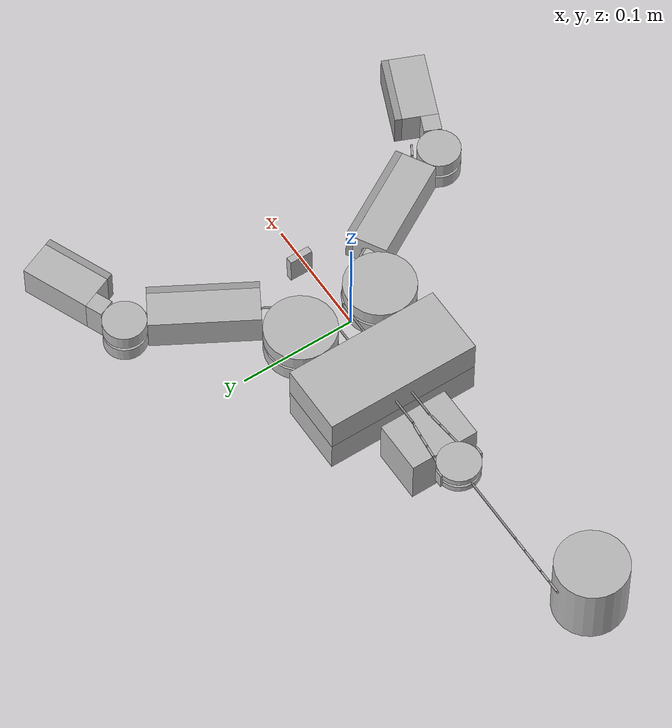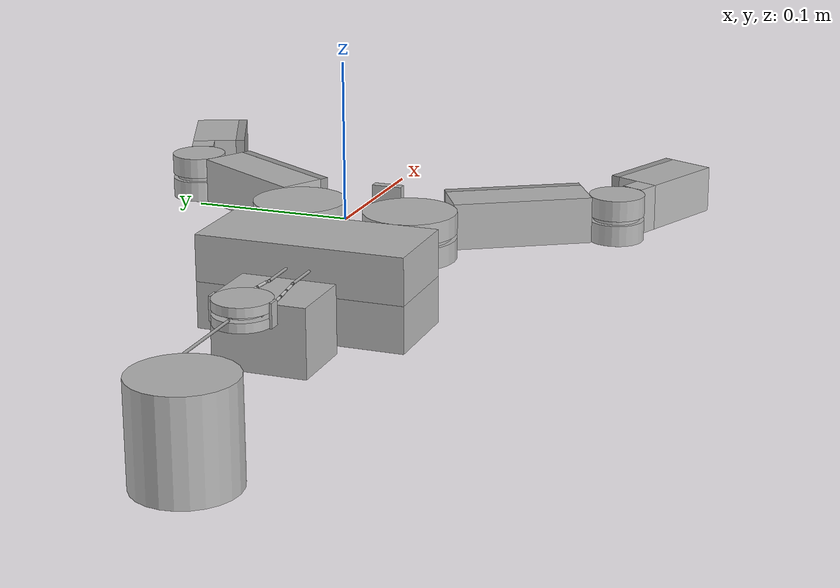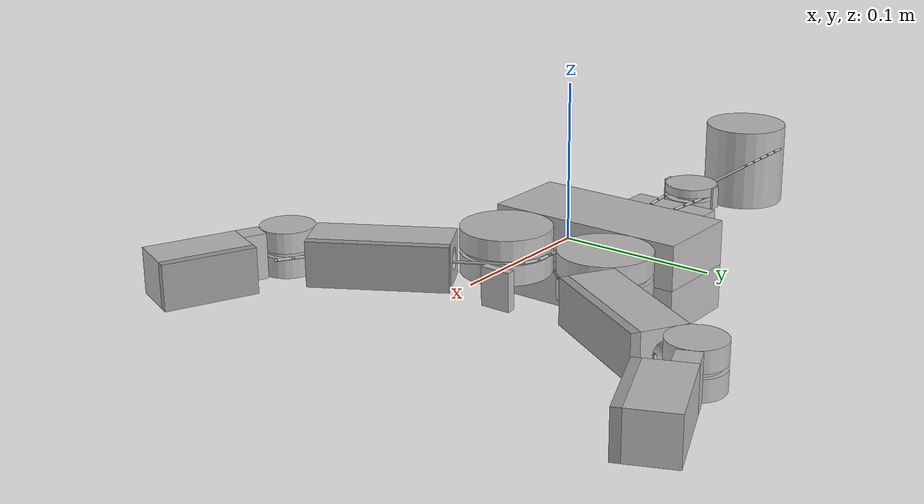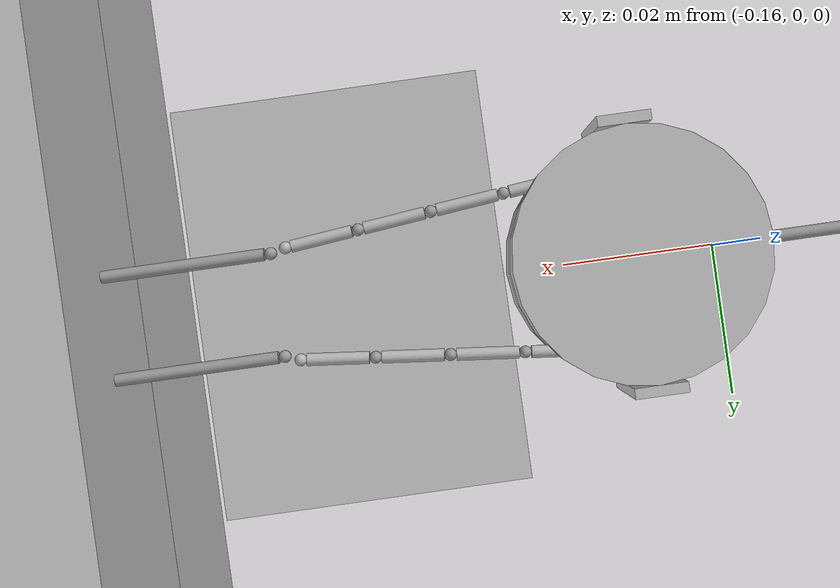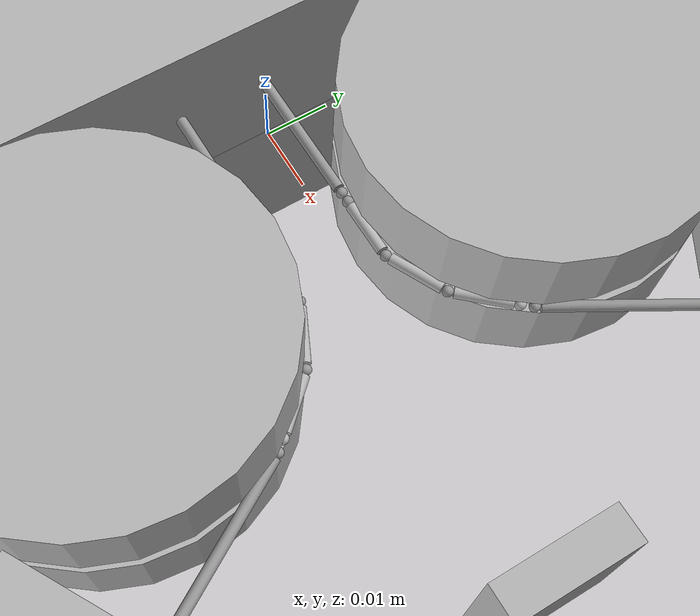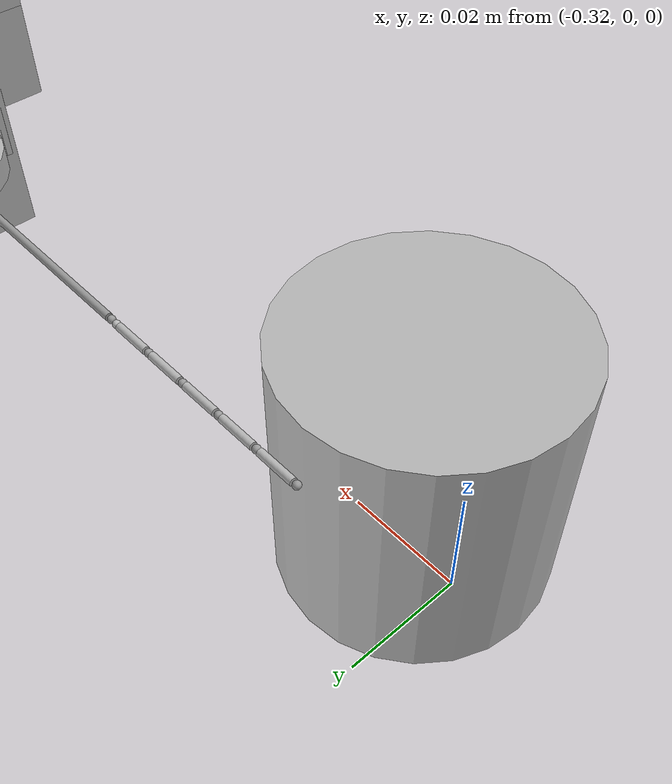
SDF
<?xml version="1.0" ?>
<sdf version="1.7">
<model name="gripper">
  <include>
    <uri>model://gripper_model</uri>
    <pose>0 0 -0.055 0 0 0</pose>
  </include>
  <!-- SERVO -->
  <link name="servo">
    <pose>-0.2859 -0.030899999999999997 -0.025 0 0 0</pose>
    <inertial>
      <inertia>
        <ixx>0.0001</ixx>
        <ixy>0</ixy>
        <ixz>0</ixz>
        <iyy>0.0001</iyy>
        <iyz>0</iyz>
        <izz>0.0001</izz>
    </inertia>
        <mass>0.051</mass>
    </inertial>
    <collision name="collision">
      <pose>0 0 0 0 0 0 </pose>
      <geometry>
        <cylinder>
          <radius>0.03</radius>
          <length>0.06</length>
        </cylinder>
      </geometry>
      <surface>
        <friction>
          <ode>
            <mu>0.001</mu>
            <mu2>0.001</mu2>
          </ode>
        </friction>
      </surface>
    </collision>
    <visual name="visual">
      <pose>0 0 0 0 0 0 </pose>
      <geometry>
        <cylinder>
          <radius>0.03</radius>
          <length>0.06</length>
        </cylinder>
      </geometry>
    </visual>
  </link>
  <joint name="SERVO_joint" type="revolute">
    <parent>gripper_model::riser</parent>
    <child>servo</child>
    <pose>0 0 0 0 -0 0</pose>
    <axis>
      <xyz>0 0 1</xyz>
      <limit>
        <lower>0</lower>
        <upper>2.44346</upper>
        <velocity>0.00005</velocity>
        <effort>10</effort>
      </limit>
      <dynamics>
        <spring_reference>0</spring_reference>
        <spring_stiffness>0.0</spring_stiffness>
        <damping>0.00</damping>
      </dynamics>
    </axis>
    <sensor name="force_torque" type="force_torque">
      <update_rate>30</update_rate>
      <force_torque>
        <frame>child</frame>
        <measure_direction>child_to_parent</measure_direction>
      </force_torque>
    </sensor>
  </joint>
  <include>
    <uri>model://cable_modelD</uri>
    <name>servo_cable</name>
    <pose>-0.285 0 -0.025 0 0 0</pose>
  </include>
  <joint name="servo_cable_joint" type="ball">
    <parent>servo</parent>
    <child>servo_cable::segment_1_sphere</child>
  </joint>
  <include>
    <uri>model://cable_modelB</uri>
    <name>servo_cable2</name>
    <pose>-0.2292 0 -0.055 0 0 0</pose>
  </include>
  <joint name="pris1" type="prismatic">
    <parent>gripper_model::riser</parent>
    <child>servo_cable2::segment_1_cylinder</child>
    <axis>
      <xyz>0 0 1</xyz>
    </axis>
  </joint>
  <joint name="servo_cable_joint2" type="ball">
    <parent>servo_cable::end_sphere</parent>
    <child>servo_cable2::segment_1_sphere</child>
  </joint>
  <link name="box_link">
    <pose>-0.11009999999999999 0 -0.03325 0 0 0</pose>
    <inertial>
      <inertia>
        <ixx>2.4299999999999994e-06</ixx>
        <ixy>0</ixy>
        <ixz>0</ixz>
        <iyy>2.4299999999999994e-06</iyy>
        <iyz>0</iyz>
        <izz>2.4299999999999994e-06</izz>
      </inertia>
      <mass>0.005399999999999999</mass>
    </inertial>
    <collision name="collision">
      <geometry>
        <box>
          <size>0.045 0.06 0.0435</size>
        </box>
      </geometry>
      <surface>
        <friction>
          <ode>
            <mu>0.001</mu>
            <mu2>0.001</mu2>
          </ode>
        </friction>
      </surface>
    </collision>
    <visual name="visual">
      <geometry>
        <box>
          <size>0.045 0.06 0.0435</size>
        </box>
      </geometry>
    </visual>
  </link>
  <joint name="box_joint" type="fixed">
    <parent>gripper_model::riser</parent>
    <child>box_link</child>
  </joint>
  <!-- PULLEY -->
  <include>
    <uri>model://pulley</uri>
    <name>pulley</name>
    <pose>-0.15131999999999998 0 -0.025 0 0 0</pose>
  </include>
  <joint name="PULLEY_joint" type="prismatic">
    <parent>gripper_model::riser</parent>
    <child>pulley::bottom</child>
    <axis>
      <xyz>1 0 0</xyz>
      <limit>
        <lower>-30.0</lower>
        <upper>0.2</upper>
      </limit>
      <dynamics>
        <spring_reference>0</spring_reference>
        <spring_stiffness>0.0</spring_stiffness>
      </dynamics>
    </axis>
  </joint>
  <joint name="pulley_servo_cable" type="fixed">
    <parent>servo_cable2::end_sphere</parent>
    <child>pulley::top</child>
  </joint>
  <joint name="pulley_servo_cablea" type="fixed">
    <parent>servo_cable::end_sphere</parent>
    <child>pulley::bottom</child>
  </joint>
  <include>
    <uri>model://cable_modelD</uri>
    <name>pulley_left_cable_model</name>
    <pose>-0.15552 0.0138 -0.025 0 0 -0.10472</pose>
  </include>
  <joint name="ball_joint_pulley_left" type="ball">
    <parent>pulley::bearing</parent>
    <child>pulley_left_cable_model::segment_1_sphere</child>
    <pose>0 0 0 0 -0 0</pose>
  </joint>
  <joint name="joint_pulley_left" type="ball">
    <parent>pulley_left_cable_model::end_sphere</parent>
    <child>straight_left_cable_model3c::end_sphere</child>
    <pose>0 0 0 0 -0 0</pose>
  </joint>
  <include>
    <uri>model://cable_modelD</uri>
    <name>pulley_right_cable_model</name>
    <pose>-0.15552 -0.0138 -0.025 0 0 0.10472</pose>
  </include>
  <joint name="ball_joint_pulley_right" type="ball">
    <parent>pulley::bearing</parent>
    <child>pulley_right_cable_model::segment_1_sphere</child>
    <pose>0 0 0 0 -0 0</pose>
  </joint>
  <joint name="joint_pulley_right" type="ball">
    <parent>pulley_right_cable_model::end_sphere</parent>
    <child>straight_right_cable_model3c::end_sphere</child>
    <pose>0 0 0 0 -0 0</pose>
  </joint>
  <!-- GRIPPER -->
  <!-- LEFT SIDE -->
  <!-- cable joints -->
  <include>
    <uri>model://cable_modelA</uri>
    <name>straight_left_cable_model3c</name>
    <pose>0.0093 0.0075 -0.055 0 0 3.14159</pose>
  </include>
  <joint name="pris2" type="prismatic">
    <parent>gripper_model::riser</parent>
    <child>straight_left_cable_model3c::segment_1_cylinder</child>
    <axis>
      <xyz>0 0 1</xyz>
      <limit>
        <lower>-1.0</lower>
        <upper>0</upper>
      </limit>
    </axis>
  </joint>
  <include>
    <uri>model://cable_modelE</uri>
    <name>curved_left_cable_model6</name>
    <pose>0.011099999999999999 0.0075 -0.025 0 0 0</pose>
  </include>
  <include>
    <uri>model://cable_modelA</uri>
    <name>left_cable_model4</name>
    <pose>0.0402 0.0219 -0.055 0 0 1.0472</pose>
  </include>
  <include>
    <uri>model://cable_modelC</uri>
    <name>left_cable_model3a</name>
    <pose>0.096 0.1176 -0.025 0 0 1.0472</pose>
  </include>
  <joint name="ball_joint_left" type="ball">
    <parent>straight_left_cable_model3c::segment_1_sphere</parent>
    <child>curved_left_cable_model6::segment_1_sphere</child>
    <pose>0 0 0 0 -0 0</pose>
  </joint>
  <joint name="ball_joint_link_left" type="ball">
    <parent>curved_left_cable_model6::end_sphere</parent>
    <child>left_cable_model4::segment_1_sphere</child>
    <pose>0 0 0 0 -0 0</pose>
  </joint>
  <joint name="ball_joint_tip_left" type="ball">
    <parent>left_cable_model4::end_sphere</parent>
    <child>left_cable_model3a::segment_1_sphere</child>
    <pose>0 0 0 0 -0 0</pose>
  </joint>
  <!-- end joints -->
  <joint name="revolute_joint_left" type="ball">
    <parent>left_cable_model3a::end_sphere</parent>
    <child>gripper_model::left_finger_tip</child>
    <pose frame ="gripper_model::left_finger_tip">0.009 -0.045 0 0 -0 0</pose>
    <axis>
      <xyz>0 0 1</xyz>
    </axis>
  </joint>
  <!-- RIGHT SIDE -->
  <!-- cable joints -->
  <include>
    <uri>model://cable_modelA</uri>
    <name>straight_right_cable_model3c</name>
    <pose>0.0093 -0.0075 -0.055 0 0 3.14159</pose>
  </include>
  <joint name="pris3" type="prismatic">
    <parent>gripper_model::riser</parent>
    <child>straight_right_cable_model3c::segment_1_cylinder</child>
    <axis>
      <xyz>0 0 1</xyz>
      <limit>
        <lower>-1.0</lower>
        <upper>0</upper>
      </limit>
    </axis>
  </joint>
  <include>
    <uri>model://cable_modelE</uri>
    <name>curved_right_cable_model5</name>
    <pose>0.011099999999999999 -0.0075 0.005 3.14159 0 0</pose>
  </include>
  <include>
    <uri>model://cable_modelA</uri>
    <name>right_cable_model4</name>
    <pose>0.0402 -0.0219 -0.055 0 0 -1.0472</pose>
  </include>
  <include>
    <uri>model://cable_modelC</uri>
    <name>right_cable_model3a</name>
    <pose>0.096 -0.1176 0.005 3.14159 0 -1.0472</pose>
  </include>
  <joint name="ball_joint_right" type="ball">
    <parent>straight_right_cable_model3c::segment_1_sphere</parent>
    <child>curved_right_cable_model5::segment_1_sphere</child>
    <pose>0 0 0 0 -0 0</pose>
  </joint>
  <joint name="ball_joint_link_right" type="ball">
    <parent>curved_right_cable_model5::end_sphere</parent>
    <child>right_cable_model4::segment_1_sphere</child>
    <pose>0 0 0 0 -0 0</pose>
  </joint>
  <joint name="ball_joint_tip_right" type="ball">
    <parent>right_cable_model4::end_sphere</parent>
    <child>right_cable_model3a::segment_1_sphere</child>
    <pose>0 0 0 0 -0 0</pose>
  </joint>
  <!-- end joints -->
  <joint name="revolute_joint_right" type="ball">
    <parent>right_cable_model3a::end_sphere</parent>
    <child>gripper_model::right_finger_tip</child>
    <pose frame ="gripper_model::right_finger_tip">0.009 0.045 0 0 0 -0 0</pose>
    <axis>
      <xyz>0 0 1</xyz>
    </axis>
  </joint>
</model>
</sdf>

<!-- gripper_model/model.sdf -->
<sdf version="1.7">
<model name="gripper_model">
  <link name="base">
    <pose>-0.045 0.0 0.015 0 0 0</pose>
    <inertial>
      <inertia>
        <ixx>3.0466176e-05</ixx>
        <ixy>0</ixy>
        <ixz>0</ixz>
        <iyy>3.0466176e-05</iyy>
        <iyz>0</iyz>
        <izz>3.0466176e-05</izz>
      </inertia>
      <mass>0.02</mass>
    </inertial>
    <collision name="collision">
      <pose>0 0 0 0 0 0</pose>
      <geometry>
        <box>
          <size>0.06 0.135 0.03</size>
        </box>
      </geometry>
    </collision>
    <visual name="visual">
      <geometry>
        <box>
          <size>0.06 0.135 0.03</size>
        </box>
      </geometry>
    </visual>
  </link>
  <link name="riser">
    <pose>-0.045 0.0 0.045 0 0 0</pose>
    <inertial>
      <inertia>
        <ixx>3.0466176e-05</ixx>
        <ixy>0</ixy>
        <ixz>0</ixz>
        <iyy>3.0466176e-05</iyy>
        <iyz>0</iyz>
        <izz>3.0466176e-05</izz>
      </inertia>
      <mass>0.02</mass>
    </inertial>
    <collision name="collisiontop">
      <pose>0 0 0.00825 1.57 0 0</pose>
      <geometry>
        <box>
          <size>0.06 0.0135 0.018</size>
        </box>
      </geometry>
    </collision>
    <collision name="collisionbottom">
      <pose>0 0 -0.00825 1.57 0 0</pose>
      <geometry>
        <box>
          <size>0.06 0.0135 0.018</size>
        </box>
      </geometry>
    </collision>
    <collision name="collisionleft">
      <pose>0 0.0195 0 1.57 0 0</pose>
      <geometry>
        <box>
          <size>0.06 0.03 0.021</size>
        </box>
      </geometry>
    </collision>
    <collision name="collisionright">
      <pose>0 -0.0195 0 1.57 0 0</pose>
      <geometry>
        <box>
          <size>0.06 0.03 0.021</size>
        </box>
      </geometry>
    </collision>
    <collision name="collisionmiddle">
      <pose>0 0 0 1.57 0 0</pose>
      <geometry>
        <box>
          <size>0.06 0.003 0.012</size>
        </box>
      </geometry>
    </collision>
    <visual name="visual">
      <geometry>
        <box>
          <size>0.06 0.135 0.03</size>
        </box>
      </geometry>
    </visual>
    <self_collide>1</self_collide>
  </link>
  <link name="palm">
    <pose>0.064 0.0 0.045 0 0 0</pose>
    <inertial>
      <inertia>
        <ixx>3.0466176e-05</ixx>
        <ixy>0</ixy>
        <ixz>0</ixz>
        <iyy>3.0466176e-05</iyy>
        <iyz>0</iyz>
        <izz>3.0466176e-05</izz>
      </inertia>
      <mass>0.015</mass>
    </inertial>
    <collision name="collision">
      <pose>0.010 0 0 0 0 0</pose>
      <geometry>
        <box>
          <size>0.006 0.02 0.025</size>
        </box>
      </geometry>
    </collision>
    <visual name="visual">
      <pose>0.010 0 0 0 0 0</pose>
      <geometry>
        <box>
          <size>0.006 0.02 0.025</size>
        </box>
      </geometry>
    </visual>
    <self_collide>1</self_collide>
    <sensor name='contact_sensor' type='contact'>
      <update_rate>20</update_rate>
      <contact>
        <collision>collision</collision>
      </contact>
      <plugin name="contact_plugin" filename="/opt/ros/noetic/lib/libgazebo_ros_bumper.so">
        <bumperTopicName>contactsensor</bumperTopicName>
        <frameName>world</frameName>
      </plugin>
    </sensor>
  </link>
  <joint name="fix_palm" type="fixed">
    <child>palm</child>
    <parent>riser</parent>
  </joint>
  <link name="left_finger_link">
    <pose relative_to="riser">0.06 0.0375 0 0 0 -0.52359</pose>
    <inertial>
      <inertia>
        <ixx>3.0466176e-05</ixx>
        <ixy>0</ixy>
        <ixz>0</ixz>
        <iyy>3.0466176e-05</iyy>
        <iyz>0</iyz>
        <izz>3.0466176e-05</izz>
      </inertia>
      <mass>0.015</mass>
    </inertial>
    <collision name="collisiontop">
      <pose>0 0 0.00825 0 0 0</pose>
      <geometry>
        <cylinder>
          <radius>0.03</radius>
          <length>0.0135</length>
        </cylinder>
      </geometry>
    </collision>
    <collision name="collisionmiddle">
      <geometry>
        <cylinder>
          <radius>0.027</radius>
          <length>0.003</length>
        </cylinder>
      </geometry>
    </collision>
    <collision name="collisionbottom">
      <pose>0 0 -0.00825 0 0 0</pose>
      <geometry>
        <cylinder>
          <radius>0.03</radius>
          <length>0.0135</length>
        </cylinder>
      </geometry>
    </collision>
    <visual name="visualtop">
      <pose>0 0 0.00825 0 0 0</pose>
      <geometry>
        <cylinder>
          <radius>0.03</radius>
          <length>0.0135</length>
        </cylinder>
      </geometry>
    </visual>
    <visual name="visualmiddle">
      <geometry>
        <cylinder>
          <radius>0.027</radius>
          <length>0.003</length>
        </cylinder>
      </geometry>
    </visual>
    <visual name="visualbottom">
      <pose>0 0 -0.00825 0 0 0</pose>
      <geometry>
        <cylinder>
          <radius>0.03</radius>
          <length>0.0135</length>
        </cylinder>
      </geometry>
    </visual>
    <self_collide>1</self_collide>
  </link>
  <link name="left_finger">
    <pose relative_to="left_finger_link">0.024 0.075 0 0 0 0</pose>
    <inertial>
      <inertia>
        <ixx>3.0466176e-05</ixx>
        <ixy>0</ixy>
        <ixz>0</ixz>
        <iyy>3.0466176e-05</iyy>
        <iyz>0</iyz>
        <izz>3.0466176e-05</izz>
      </inertia>
      <mass>0.015</mass>
    </inertial>
    <collision name="collisionleft">
      <pose>0.01125 0 0 1.57 0 0</pose>
      <geometry>
        <box>
          <size>0.0075 0.03 0.09</size>
        </box>
      </geometry>
    </collision>
    <collision name="collisionright">
      <pose>-0.01125 0 0 1.57 0 0</pose>
      <geometry>
        <box>
          <size>0.0075 0.03 0.09</size>
        </box>
      </geometry>
    </collision>
    <collision name="collisiontop">
      <pose>0 0 0.00825 1.57 0 0</pose>
      <geometry>
        <box>
          <size>0.015 0.0135 0.09</size>
        </box>
      </geometry>
    </collision>
    <collision name="collisionbottom">
      <pose>0 0 -0.00825 1.57 0 0</pose>
      <geometry>
        <box>
          <size>0.015 0.0135 0.09</size>
        </box>
      </geometry>
    </collision>
    <visual name="visual">
      <pose>0 0 0 1.57 0 0</pose>
      <geometry>
        <mesh>
          <scale>0.3 0.3 0.3</scale>
          <uri>model://gripper_model/meshes/gripper_finger.stl</uri>
        </mesh>
      </geometry>
    </visual>
    <self_collide>1</self_collide>
  </link>
  <link name="soft_left_finger_pad">
    <pose relative_to="left_finger">0.018 0 0 1.5708 0 1.5708</pose>
    <inertial>
      <pose>0 0 0 0 0 0</pose>
      <inertia>
        <ixx>3.046617599999999e-06</ixx>
        <ixy>0</ixy>
        <ixz>0</ixz>
        <iyy>3.046617599999999e-06</iyy>
        <iyz>0</iyz>
        <izz>3.046617599999999e-06</izz>
      </inertia>
      <mass>0.003</mass>
    </inertial>
    <collision name="collision">
      <geometry>
        <box>
          <size>0.09 0.03 0.006</size>
        </box>
      </geometry>
      <surface>
        <contact>
          <ode>
            <soft_erp>0.2</soft_erp>
            <kp>1400</kp>
            <kd>0.5</kd>
            <max_vel>0.2</max_vel>
            <min_depth>0.05</min_depth>
          </ode>
        </contact>
        <friction>
          <ode>
            <mu>5.0</mu>
            <mu2>5.0</mu2>
          </ode>
        </friction>
      </surface>
    </collision>
    <visual name="visual">
      <geometry>
        <box>
          <size>0.09 0.03 0.006</size>
        </box>
      </geometry>
      <material>
        <script>
          <name>Gazebo/Gray</name>
          <uri>file://media/materials/scripts/gazebo.material</uri>
        </script>
      </material>
    </visual>
  </link>
  <link name="left_finger_tip_link">
    <pose relative_to="left_finger">-0.009 0.063 0 0 0 -0.645772</pose>
    <inertial>
      <inertia>
        <ixx>3.0466176e-05</ixx>
        <ixy>0</ixy>
        <ixz>0</ixz>
        <iyy>3.0466176e-05</iyy>
        <iyz>0</iyz>
        <izz>3.0466176e-05</izz>
      </inertia>
      <mass>0.015</mass>
    </inertial>
    <collision name="collisiontop">
      <pose>0 0 0.00825 0 0 0</pose>
      <geometry>
        <cylinder>
          <radius>0.018</radius>
          <length>0.0135</length>
        </cylinder>
      </geometry>
    </collision>
    <collision name="collisionmiddle">
      <geometry>
        <cylinder>
          <radius>0.015</radius>
          <length>0.003</length>
        </cylinder>
      </geometry>
    </collision>
    <collision name="collisionbottom">
      <pose>0 0 -0.00825 0 0 0</pose>
      <geometry>
        <cylinder>
          <radius>0.018</radius>
          <length>0.0135</length>
        </cylinder>
      </geometry>
    </collision>
    <visual name="visualtop">
      <pose>0 0 0.00825 0 0 0</pose>
      <geometry>
        <cylinder>
          <radius>0.018</radius>
          <length>0.0135</length>
        </cylinder>
      </geometry>
    </visual>
    <visual name="visualmiddle">
      <geometry>
        <cylinder>
          <radius>0.015</radius>
          <length>0.003</length>
        </cylinder>
      </geometry>
    </visual>
    <visual name="visualbottom">
      <pose>0 0 -0.00825 0 0 0</pose>
      <geometry>
        <cylinder>
          <radius>0.018</radius>
          <length>0.0135</length>
        </cylinder>
      </geometry>
    </visual>
  </link>
  <link name="left_finger_tip_spacer">
    <pose relative_to="left_finger_tip_link">0.0015 0.025500000000000002 0 0 0 0</pose>
    <inertial>
      <inertia>
        <ixx>3.046617599999999e-06</ixx>
        <ixy>0</ixy>
        <ixz>0</ixz>
        <iyy>3.046617599999999e-06</iyy>
        <iyz>0</iyz>
        <izz>3.046617599999999e-06</izz>
      </inertia>
      <mass>0.003</mass>
    </inertial>
    <collision name="collision">
      <geometry>
        <box>
          <size>0.015 0.015 0.03</size>
        </box>
      </geometry>
    </collision>
    <visual name="visual">
      <geometry>
        <box>
          <size>0.015 0.015 0.03</size>
        </box>
      </geometry>
    </visual>
  </link>
  <link name="left_finger_tip">
    <pose relative_to="left_finger_tip_link">0.009 0.063 0 0 0 0</pose>
    <inertial>
      <inertia>
        <ixx>3.0466176e-05</ixx>
        <ixy>0</ixy>
        <ixz>0</ixz>
        <iyy>3.0466176e-05</iyy>
        <iyz>0</iyz>
        <izz>3.0466176e-05</izz>
      </inertia>
      <mass>0.015</mass>
    </inertial>
    <collision name="collision">
      <geometry>
        <box>
          <size>0.03 0.06 0.03</size>
        </box>
      </geometry>
    </collision>
    <visual name="visual">
      <geometry>
        <box>
          <size>0.03 0.06 0.03</size>
        </box>
      </geometry>
    </visual>
    <self_collide>1</self_collide>
  </link>
  <link name="soft_left_fingertip_pad">
    <pose relative_to="left_finger_tip">0.018 0 0 1.5708 0 1.5708</pose>
    <inertial>
      <pose>0 0 0 0 0 0</pose>
      <inertia>
        <ixx>3.046617599999999e-06</ixx>
        <ixy>0</ixy>
        <ixz>0</ixz>
        <iyy>3.046617599999999e-06</iyy>
        <iyz>0</iyz>
        <izz>3.046617599999999e-06</izz>
      </inertia>
      <mass>0.003</mass>
    </inertial>
    <collision name="collision">
      <geometry>
        <box>
          <size>0.06 0.03 0.006</size>
        </box>
      </geometry>
      <surface>
        <contact>
          <ode>
            <soft_cfm>0.5</soft_cfm>
            <soft_erp>0.2</soft_erp>
            <kp>1400</kp>
            <kd>0.5</kd>
            <max_vel>0.2</max_vel>
            <min_depth>0.05</min_depth>
          </ode>
        </contact>
        <friction>
          <ode>
            <mu>5.0</mu>
            <mu2>5.0</mu2>
          </ode>
        </friction>
      </surface>
    </collision>
    <visual name="visual">
      <geometry>
        <box>
          <size>0.06 0.03 0.006</size>
        </box>
      </geometry>
      <material>
        <script>
          <name>Gazebo/Gray</name>
          <uri>file://media/materials/scripts/gazebo.material</uri>
        </script>
      </material>
    </visual>
  </link>
  <link name="right_finger_link">
    <pose relative_to="riser">0.06 -0.0375 0 0 0 0.52359</pose>
    <inertial>
      <inertia>
        <ixx>3.0466176e-05</ixx>
        <ixy>0</ixy>
        <ixz>0</ixz>
        <iyy>3.0466176e-05</iyy>
        <iyz>0</iyz>
        <izz>3.0466176e-05</izz>
      </inertia>
      <mass>0.015</mass>
    </inertial>
    <collision name="collisiontop">
      <pose>0 0 0.00825 0 0 0 </pose>
      <geometry>
        <cylinder>
          <radius>0.03</radius>
          <length>0.0135</length>
        </cylinder>
      </geometry>
    </collision>
    <collision name="collisionmiddle">
      <geometry>
        <cylinder>
          <radius>0.027</radius>
          <length>0.003</length>
        </cylinder>
      </geometry>
    </collision>
    <collision name="collisionbottom">
      <pose>0 0 -0.00825 0 0 0 </pose>
      <geometry>
        <cylinder>
          <radius>0.03</radius>
          <length>0.0135</length>
        </cylinder>
      </geometry>
    </collision>
    <visual name="visualtop">
      <pose>0 0 0.00825 0 0 0 </pose>
      <geometry>
        <cylinder>
          <radius>0.03</radius>
          <length>0.0135</length>
        </cylinder>
      </geometry>
    </visual>
    <visual name="visualmiddle">
      <geometry>
        <cylinder>
          <radius>0.027</radius>
          <length>0.003</length>
        </cylinder>
      </geometry>
    </visual>
    <visual name="visualbottom">
      <pose>0 0 -0.00825 0 0 0 </pose>
      <geometry>
        <cylinder>
          <radius>0.03</radius>
          <length>0.0135</length>
        </cylinder>
      </geometry>
    </visual>
    <self_collide>1</self_collide>
  </link>
  <link name="right_finger">
    <pose relative_to="right_finger_link">0.024 -0.075 0 0 0 0</pose>
    <inertial>
      <inertia>
        <ixx>3.0466176e-05</ixx>
        <ixy>0</ixy>
        <ixz>0</ixz>
        <iyy>3.0466176e-05</iyy>
        <iyz>0</iyz>
        <izz>3.0466176e-05</izz>
      </inertia>
      <mass>0.015</mass>
    </inertial>
    <collision name="collisionleft">
      <pose>0.01125 0 0 1.57 0 0</pose>
      <geometry>
        <box>
          <size>0.0075 0.03 0.09</size>
        </box>
      </geometry>
    </collision>
    <collision name="collisionright">
      <pose>-0.01125 0 0 1.57 0 0</pose>
      <geometry>
        <box>
          <size>0.0075 0.03 0.09</size>
        </box>
      </geometry>
    </collision>
    <collision name="collisiontop">
      <pose>0 0 0.00825 1.57 0 0</pose>
      <geometry>
        <box>
          <size>0.015 0.0135 0.09</size>
        </box>
      </geometry>
    </collision>
    <collision name="collisionbottom">
      <pose>0 0 -0.00825 1.57 0 0</pose>
      <geometry>
        <box>
          <size>0.015 0.0135 0.09</size>
        </box>
      </geometry>
    </collision>
    <visual name="visual">
      <pose>0 0 0 1.57 0 0</pose>
      <geometry>
        <mesh>
          <scale>0.3 0.3 0.3</scale>
          <uri>model://gripper_model/meshes/gripper_finger.stl</uri>
        </mesh>
      </geometry>
    </visual>
    <self_collide>1</self_collide>
  </link>
  <link name="soft_right_finger_pad">
    <pose relative_to="right_finger">0.018 0 0 1.5708 0 1.5708</pose>
    <inertial>
      <pose>0 0 0 0 0 0</pose>
      <inertia>
        <ixx>3.046617599999999e-06</ixx>
        <ixy>0</ixy>
        <ixz>0</ixz>
        <iyy>3.046617599999999e-06</iyy>
        <iyz>0</iyz>
        <izz>3.046617599999999e-06</izz>
      </inertia>
      <mass>0.003</mass>
    </inertial>
    <collision name="collision">
      <geometry>
        <box>
          <size>0.09 0.03 0.006</size>
        </box>
      </geometry>
      <surface>
        <contact>
          <ode>
            <soft_cfm>0.5</soft_cfm>
            <soft_erp>0.2</soft_erp>
            <kp>1400</kp>
            <kd>0.5</kd>
            <max_vel>0.2</max_vel>
            <min_depth>0.05</min_depth>
          </ode>
        </contact>
        <friction>
          <ode>
            <mu>5.0</mu>
            <mu2>5.0</mu2>
          </ode>
        </friction>
      </surface>
    </collision>
    <visual name="visual">
      <geometry>
        <box>
          <size>0.09 0.03 0.006</size>
        </box>
      </geometry>
      <material>
        <script>
          <name>Gazebo/Gray</name>
          <uri>file://media/materials/scripts/gazebo.material</uri>
        </script>
      </material>
    </visual>
  </link>
  <link name="right_finger_tip_link">
    <pose relative_to="right_finger">-0.009 -0.063 0 0 0 0.645772</pose>
    <inertial>
      <inertia>
        <ixx>3.0466176e-05</ixx>
        <ixy>0</ixy>
        <ixz>0</ixz>
        <iyy>3.0466176e-05</iyy>
        <iyz>0</iyz>
        <izz>3.0466176e-05</izz>
      </inertia>
      <mass>0.015</mass>
    </inertial>
    <collision name="collisiontop">
      <pose>0 0 0.00825 0 0 0 </pose>
      <geometry>
        <cylinder>
          <radius>0.018</radius>
          <length>0.0135</length>
        </cylinder>
      </geometry>
    </collision>
    <collision name="collisionmiddle">
      <geometry>
        <cylinder>
          <radius>0.015</radius>
          <length>0.003</length>
        </cylinder>
      </geometry>
    </collision>
    <collision name="collisionbottom">
      <pose>0 0 -0.00825 0 0 0 </pose>
      <geometry>
        <cylinder>
          <radius>0.018</radius>
          <length>0.0135</length>
        </cylinder>
      </geometry>
    </collision>
    <visual name="visualtop">
      <pose>0 0 0.00825 0 0 0 </pose>
      <geometry>
        <cylinder>
          <radius>0.018</radius>
          <length>0.0135</length>
        </cylinder>
      </geometry>
    </visual>
    <visual name="visualmiddle">
      <geometry>
        <cylinder>
          <radius>0.015</radius>
          <length>0.003</length>
        </cylinder>
      </geometry>
    </visual>
    <visual name="visualbottom">
      <pose>0 0 -0.00825 0 0 0 </pose>
      <geometry>
        <cylinder>
          <radius>0.018</radius>
          <length>0.0135</length>
        </cylinder>
      </geometry>
    </visual>
  </link>
  <link name="right_finger_tip_spacer">
    <pose relative_to="right_finger_tip_link">0.0015 -0.025500000000000002 0 0 0 0</pose>
    <inertial>
      <inertia>
        <ixx>3.046617599999999e-06</ixx>
        <ixy>0</ixy>
        <ixz>0</ixz>
        <iyy>3.046617599999999e-06</iyy>
        <iyz>0</iyz>
        <izz>3.046617599999999e-06</izz>
      </inertia>
      <mass>0.003</mass>
    </inertial>
    <collision name="collision">
      <geometry>
        <box>
          <size>0.015 0.015 0.03</size>
        </box>
      </geometry>
    </collision>
    <visual name="visual">
      <geometry>
        <box>
          <size>0.015 0.015 0.03</size>
        </box>
      </geometry>
    </visual>
  </link>
  <link name="right_finger_tip">
    <pose relative_to="right_finger_tip_link">0.009 -0.063 0 0 0 0</pose>
    <inertial>
      <inertia>
        <ixx>3.0466176e-05</ixx>
        <ixy>0</ixy>
        <ixz>0</ixz>
        <iyy>3.0466176e-05</iyy>
        <iyz>0</iyz>
        <izz>3.0466176e-05</izz>
      </inertia>
      <mass>0.015</mass>
    </inertial>
    <collision name="collision">
      <geometry>
        <box>
          <size>0.03 0.06 0.03</size>
        </box>
      </geometry>
    </collision>
    <visual name="visual">
      <geometry>
        <box>
          <size>0.03 0.06 0.03</size>
        </box>
      </geometry>
    </visual>
    <self_collide>1</self_collide>
  </link>
  <link name="soft_right_fingertip_pad">
    <pose relative_to="right_finger_tip">0.018 0 0 1.5708 0 1.5708</pose>
    <inertial>
      <pose>0 0 0 0 0 0</pose>
      <inertia>
        <ixx>3.046617599999999e-06</ixx>
        <ixy>0</ixy>
        <ixz>0</ixz>
        <iyy>3.046617599999999e-06</iyy>
        <iyz>0</iyz>
        <izz>3.046617599999999e-06</izz>
      </inertia>
      <mass>0.003</mass>
    </inertial>
    <collision name="collision">
      <geometry>
        <box>
          <size>0.06 0.03 0.006</size>
        </box>
      </geometry>
      <surface>
        <contact>
          <ode>
            <soft_cfm>0.5</soft_cfm>
            <soft_erp>0.2</soft_erp>
            <kp>1400</kp>
            <kd>0.5</kd>
            <max_vel>0.2</max_vel>
            <min_depth>0.05</min_depth>
          </ode>
        </contact>
        <friction>
          <ode>
            <mu>5.0</mu>
            <mu2>5.0</mu2>
          </ode>
        </friction>
      </surface>
    </collision>
    <visual name="visual">
      <geometry>
        <box>
          <size>0.06 0.03 0.006</size>
        </box>
      </geometry>
      <material>
        <script>
          <name>Gazebo/Gray</name>
          <uri>file://media/materials/scripts/gazebo.material</uri>
        </script>
      </material>
    </visual>
  </link>
  <static>false</static>
  <!-- JOINTS -->
  <joint name="base_riser" type="fixed">
    <child>riser</child>
    <parent>base</parent>
  </joint>
  <joint name="riser_left_finger_link" type="revolute">
    <child>left_finger_link</child>
    <parent>riser</parent>
    <axis>
      <limit>
        <lower>-0.95</lower>
        <upper>0.28</upper>
      </limit>
      <xyz>0 0 1</xyz>
      <dynamics>
        <spring_reference>0</spring_reference>
        <spring_stiffness>0.09</spring_stiffness>
        <damping>0.1</damping>
      </dynamics>
    </axis>
    <sensor name="force_torque1" type="force_torque">
      <update_rate>30</update_rate>
      <force_torque>
        <frame>child</frame>
        <measure_direction>child_to_parent</measure_direction>
      </force_torque>
    </sensor>
  </joint>
  <joint name="fix_left_finger_link" type="fixed">
    <child>left_finger</child>
    <parent>left_finger_link</parent>
  </joint>
  <joint name="joint_left_finger_tip_link" type="revolute">
    <child>left_finger_tip_link</child>
    <parent>left_finger</parent>
    <axis>
      <limit>
        <lower>-0.90</lower>
        <upper>0.17</upper>
      </limit>
      <xyz>0 0 1</xyz>
      <dynamics>
        <spring_reference>0</spring_reference>
        <spring_stiffness>0.09</spring_stiffness>
        <damping>0.1</damping>
      </dynamics>
    </axis>
    <sensor name="force_torque2" type="force_torque">
      <update_rate>30</update_rate>
      <force_torque>
        <frame>child</frame>
        <measure_direction>child_to_parent</measure_direction>
      </force_torque>
    </sensor>
  </joint>
  <joint name="fix_left_finger_tip_link" type="fixed">
    <child>left_finger_tip</child>
    <parent>left_finger_tip_link</parent>
  </joint>
  <joint name="fix_left_finger_tip_spacer" type="fixed">
    <child>left_finger_tip</child>
    <parent>left_finger_tip_spacer</parent>
  </joint>
  <joint name="riser_right_finger_link" type="revolute">
    <child>right_finger_link</child>
    <parent>riser</parent>
    <axis>
      <limit>
        <lower>-0.28</lower>
        <upper>0.95</upper>
      </limit>
      <xyz>0 0 1</xyz>
      <dynamics>
        <spring_reference>0</spring_reference>
        <spring_stiffness>0.09</spring_stiffness>
        <damping>0.1</damping>
      </dynamics>
    </axis>
    <sensor name="force_torque3" type="force_torque">
      <update_rate>30</update_rate>
      <force_torque>
        <frame>child</frame>
        <measure_direction>child_to_parent</measure_direction>
      </force_torque>
    </sensor>
  </joint>
  <joint name="fix_right_finger_link" type="fixed">
    <child>right_finger</child>
    <parent>right_finger_link</parent>
  </joint>
  <joint name="joint_right_finger_tip_link" type="revolute">
    <child>right_finger_tip_link</child>
    <parent>right_finger</parent>
    <axis>
      <limit>
        <lower>-0.17</lower>
        <upper>0.90</upper>
      </limit>
      <xyz>0 0 1</xyz>
      <dynamics>
        <spring_reference>0</spring_reference>
        <spring_stiffness>0.09</spring_stiffness>
        <damping>0.1</damping>
      </dynamics>
    </axis>
    <sensor name="force_torque4" type="force_torque">
      <update_rate>30</update_rate>
      <force_torque>
        <frame>child</frame>
        <measure_direction>child_to_parent</measure_direction>
      </force_torque>
    </sensor>
  </joint>
  <joint name="fix_right_finger_tip_link" type="fixed">
    <child>right_finger_tip</child>
    <parent>right_finger_tip_link</parent>
  </joint>
  <joint name="fix_right_finger_tip_spacer" type="fixed">
    <child>right_finger_tip</child>
    <parent>right_finger_tip_spacer</parent>
  </joint>
  <!-- pad joints -->
  <joint name="soft_left_finger_pad_joint" type="fixed">
    <child>soft_left_finger_pad</child>
    <parent>left_finger</parent>
  </joint>
  <joint name="soft_left_fingertip_pad_joint" type="fixed">
    <child>soft_left_fingertip_pad</child>
    <parent>left_finger_tip</parent>
  </joint>
  <joint name="soft_right_finger_pad_joint" type="fixed">
    <child>soft_right_finger_pad</child>
    <parent>right_finger</parent>
  </joint>
  <joint name="soft_right_fingertip_pad_joint" type="fixed">
    <child>soft_right_fingertip_pad</child>
    <parent>right_finger_tip</parent>
  </joint>
</model>
</sdf>

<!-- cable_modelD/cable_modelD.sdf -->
<sdf version='1.7'>
<model name="cable_modelD">
  <link name="segment_1_sphere">
    <pose>0 0 0.015 1.57 -0 -1.57</pose>
    <inertial>
      <pose>0 0 0 0 -0 0</pose>
      <mass>0.0025</mass>
      <inertia>
        <ixx>0.000001</ixx>
        <ixy>0</ixy>
        <ixz>0</ixz>
        <iyy>0.000001</iyy>
        <iyz>0</iyz>
        <izz>0.000001</izz>
      </inertia>
    </inertial>
    <collision name="segment_1_sphere_collision">
      <pose>0 0 0 0 -0 0</pose>
      <geometry>
        <sphere>
          <radius>0.0009</radius>
        </sphere>
      </geometry>
      <surface>
        <friction>
          <ode>
            <mu>0.001</mu>
            <mu2>0.001</mu2>
          </ode>
        </friction>
      </surface>
    </collision>
    <visual name="segment_1_sphere_visual">
      <pose>0 0 0 0 -0 0</pose>
      <geometry>
        <sphere>
          <radius>0.0009</radius>
        </sphere>
      </geometry>
      <material>
        <script>
          <name>Gazebo/Gray</name>
          <uri>file://media/materials/scripts/gazebo.material</uri>
        </script>
      </material>
    </visual>
    <self_collide>1</self_collide>
  </link>
  <joint name="segment_1_sphere_to_cylinder" type="ball">
    <pose relative_to="segment_1_sphere">0 0 0 0 -0 0</pose>
    <parent>segment_1_sphere</parent>
    <child>segment_1_cylinder</child>
    <axis>
      <xyz>1 0 0</xyz>
      <limit>
        <lower>-3.14</lower>
        <upper>3.14</upper>
        <effort>10</effort>
        <velocity>3</velocity>
      </limit>
      <dynamics>
        <damping>0.1</damping>
        <friction>0</friction>
        <spring_reference>0</spring_reference>
        <spring_stiffness>0</spring_stiffness>
      </dynamics>
    </axis>
  </joint>
  <link name="segment_1_cylinder">
    <pose relative_to="segment_1_sphere_to_cylinder">0 0 0 0 -0 0</pose>
    <inertial>
      <pose>0 0 -0.005399999999999999 0 -0 0</pose>
      <mass>0.0025</mass>
      <inertia>
        <ixx>0.000001</ixx>
        <ixy>0</ixy>
        <ixz>0</ixz>
        <iyy>0.000001</iyy>
        <iyz>0</iyz>
        <izz>0.000001</izz>
      </inertia>
    </inertial>
    <collision name="segment_1_cylinder_collision">
      <pose>0 0 -0.005399999999999999 0 -0 0</pose>
      <geometry>
        <cylinder>
          <length>0.009</length>
          <radius>0.0009</radius>
        </cylinder>
      </geometry>
      <surface>
        <friction>
          <ode>
            <mu>0.001</mu>
            <mu2>0.001</mu2>
          </ode>
        </friction>
        <contact>
          <ode>
            <soft_cfm>0.5</soft_cfm>
            <soft_erp>0.2</soft_erp>
            <kp>1500</kp>
            <kd>0.5</kd>
            <max_vel>0.2</max_vel>
            <min_depth>0.005</min_depth>
          </ode>
        </contact>
      </surface>
    </collision>
    <visual name="segment_1_cylinder_visual">
      <pose>0 0 -0.005399999999999999 0 -0 0</pose>
      <geometry>
        <cylinder>
          <length>0.009</length>
          <radius>0.0009</radius>
        </cylinder>
      </geometry>
    </visual>
    <self_collide>1</self_collide>
  </link>
  <joint name="segment_1_cylinder_to_segment_2_sphere" type="ball">
    <pose relative_to="segment_1_cylinder">0 0 -0.010799999999999999 0 -0 0</pose>
    <parent>segment_1_cylinder</parent>
    <child>segment_2_sphere</child>
    <axis>
      <xyz>0 1 0</xyz>
      <limit>
        <lower>-3.14</lower>
        <upper>3.14</upper>
        <effort>10</effort>
        <velocity>3</velocity>
      </limit>
      <dynamics>
        <damping>0.1</damping>
        <friction>0</friction>
        <spring_reference>0</spring_reference>
        <spring_stiffness>0</spring_stiffness>
      </dynamics>
    </axis>
  </joint>
  <link name="segment_2_sphere">
    <pose relative_to="segment_1_cylinder_to_segment_2_sphere">0 0 0 0 -0 0</pose>
    <inertial>
      <pose>0 0 0 0 -0 0</pose>
      <mass>0.0025</mass>
      <inertia>
        <ixx>0.000001</ixx>
        <ixy>0</ixy>
        <ixz>0</ixz>
        <iyy>0.000001</iyy>
        <iyz>0</iyz>
        <izz>0.000001</izz>
      </inertia>
    </inertial>
    <collision name="segment_2_sphere_collision">
      <pose>0 0 0 0 -0 0</pose>
      <geometry>
        <sphere>
          <radius>0.0009</radius>
        </sphere>
      </geometry>
      <surface>
        <friction>
          <ode>
            <mu>0.001</mu>
            <mu2>0.001</mu2>
          </ode>
        </friction>
      </surface>
    </collision>
    <visual name="segment_2_sphere_visual">
      <pose>0 0 0 0 -0 0</pose>
      <geometry>
        <sphere>
          <radius>0.0009</radius>
        </sphere>
      </geometry>
      <material>
        <script>
          <name>Gazebo/Gray</name>
          <uri>file://media/materials/scripts/gazebo.material</uri>
        </script>
      </material>
    </visual>
    <self_collide>1</self_collide>
  </link>
  <joint name="segment_2_sphere_to_cylinder" type="ball">
    <pose relative_to="segment_2_sphere">0 0 0 0 -0 0</pose>
    <parent>segment_2_sphere</parent>
    <child>segment_2_cylinder</child>
    <axis>
      <xyz>1 0 0</xyz>
      <limit>
        <lower>-3.14</lower>
        <upper>3.14</upper>
        <effort>10</effort>
        <velocity>3</velocity>
      </limit>
      <dynamics>
        <damping>0.1</damping>
        <friction>0</friction>
        <spring_reference>0</spring_reference>
        <spring_stiffness>0</spring_stiffness>
      </dynamics>
    </axis>
  </joint>
  <link name="segment_2_cylinder">
    <pose relative_to="segment_2_sphere_to_cylinder">0 0 0 0 -0 0</pose>
    <inertial>
      <pose>0 0 -0.005399999999999999 0 -0 0</pose>
      <mass>0.0025</mass>
      <inertia>
        <ixx>0.000001</ixx>
        <ixy>0</ixy>
        <ixz>0</ixz>
        <iyy>0.000001</iyy>
        <iyz>0</iyz>
        <izz>0.000001</izz>
      </inertia>
    </inertial>
    <collision name="segment_2_cylinder_collision">
      <pose>0 0 -0.005399999999999999 0 -0 0</pose>
      <geometry>
        <cylinder>
          <length>0.009</length>
          <radius>0.0009</radius>
        </cylinder>
      </geometry>
      <surface>
        <friction>
          <ode>
            <mu>0.001</mu>
            <mu2>0.001</mu2>
          </ode>
        </friction>
        <contact>
          <ode>
            <soft_cfm>0.5</soft_cfm>
            <soft_erp>0.2</soft_erp>
            <kp>1500</kp>
            <kd>0.5</kd>
            <max_vel>0.2</max_vel>
            <min_depth>0.005</min_depth>
          </ode>
        </contact>
      </surface>
    </collision>
    <visual name="segment_2_cylinder_visual">
      <pose>0 0 -0.005399999999999999 0 -0 0</pose>
      <geometry>
        <cylinder>
          <length>0.009</length>
          <radius>0.0009</radius>
        </cylinder>
      </geometry>
    </visual>
    <self_collide>1</self_collide>
  </link>
  <joint name="segment_2_cylinder_to_segment_3_sphere" type="ball">
    <pose relative_to="segment_2_cylinder">0 0 -0.010799999999999999 0 -0 0</pose>
    <parent>segment_2_cylinder</parent>
    <child>segment_3_sphere</child>
    <axis>
      <xyz>0 1 0</xyz>
      <limit>
        <lower>-3.14</lower>
        <upper>3.14</upper>
        <effort>10</effort>
        <velocity>3</velocity>
      </limit>
      <dynamics>
        <damping>0.1</damping>
        <friction>0</friction>
        <spring_reference>0</spring_reference>
        <spring_stiffness>0</spring_stiffness>
      </dynamics>
    </axis>
  </joint>
  <link name="segment_3_sphere">
    <pose relative_to="segment_2_cylinder_to_segment_3_sphere">0 0 0 0 -0 0</pose>
    <inertial>
      <pose>0 0 0 0 -0 0</pose>
      <mass>0.0025</mass>
      <inertia>
        <ixx>0.000001</ixx>
        <ixy>0</ixy>
        <ixz>0</ixz>
        <iyy>0.000001</iyy>
        <iyz>0</iyz>
        <izz>0.000001</izz>
      </inertia>
    </inertial>
    <collision name="segment_3_sphere_collision">
      <pose>0 0 0 0 -0 0</pose>
      <geometry>
        <sphere>
          <radius>0.0009</radius>
        </sphere>
      </geometry>
      <surface>
        <friction>
          <ode>
            <mu>0.001</mu>
            <mu2>0.001</mu2>
          </ode>
        </friction>
      </surface>
    </collision>
    <visual name="segment_3_sphere_visual">
      <pose>0 0 0 0 -0 0</pose>
      <geometry>
        <sphere>
          <radius>0.0009</radius>
        </sphere>
      </geometry>
      <material>
        <script>
          <name>Gazebo/Gray</name>
          <uri>file://media/materials/scripts/gazebo.material</uri>
        </script>
      </material>
    </visual>
    <self_collide>1</self_collide>
  </link>
  <joint name="segment_3_sphere_to_cylinder" type="ball">
    <pose relative_to="segment_3_sphere">0 0 0 0 -0 0</pose>
    <parent>segment_3_sphere</parent>
    <child>segment_3_cylinder</child>
    <axis>
      <xyz>1 0 0</xyz>
      <limit>
        <lower>-3.14</lower>
        <upper>3.14</upper>
        <effort>10</effort>
        <velocity>3</velocity>
      </limit>
      <dynamics>
        <damping>0.1</damping>
        <friction>0</friction>
        <spring_reference>0</spring_reference>
        <spring_stiffness>0</spring_stiffness>
      </dynamics>
    </axis>
  </joint>
  <link name="segment_3_cylinder">
    <pose relative_to="segment_3_sphere_to_cylinder">0 0 0 0 -0 0</pose>
    <inertial>
      <pose>0 0 -0.005399999999999999 0 -0 0</pose>
      <mass>0.0025</mass>
      <inertia>
        <ixx>0.000001</ixx>
        <ixy>0</ixy>
        <ixz>0</ixz>
        <iyy>0.000001</iyy>
        <iyz>0</iyz>
        <izz>0.000001</izz>
      </inertia>
    </inertial>
    <collision name="segment_3_cylinder_collision">
      <pose>0 0 -0.005399999999999999 0 -0 0</pose>
      <geometry>
        <cylinder>
          <length>0.009</length>
          <radius>0.0009</radius>
        </cylinder>
      </geometry>
      <surface>
        <friction>
          <ode>
            <mu>0.001</mu>
            <mu2>0.001</mu2>
          </ode>
        </friction>
        <contact>
          <ode>
            <soft_cfm>0.5</soft_cfm>
            <soft_erp>0.2</soft_erp>
            <kp>1500</kp>
            <kd>0.5</kd>
            <max_vel>0.2</max_vel>
            <min_depth>0.005</min_depth>
          </ode>
        </contact>
      </surface>
    </collision>
    <visual name="segment_3_cylinder_visual">
      <pose>0 0 -0.005399999999999999 0 -0 0</pose>
      <geometry>
        <cylinder>
          <length>0.009</length>
          <radius>0.0009</radius>
        </cylinder>
      </geometry>
    </visual>
    <self_collide>1</self_collide>
  </link>
  <joint name="segment_3_cylinder_to_segment_4_sphere" type="ball">
    <pose relative_to="segment_3_cylinder">0 0 -0.010799999999999999 0 -0 0</pose>
    <parent>segment_3_cylinder</parent>
    <child>segment_4_sphere</child>
    <axis>
      <xyz>0 1 0</xyz>
      <limit>
        <lower>-3.14</lower>
        <upper>3.14</upper>
        <effort>10</effort>
        <velocity>3</velocity>
      </limit>
      <dynamics>
        <damping>0.1</damping>
        <friction>0</friction>
        <spring_reference>0</spring_reference>
        <spring_stiffness>0</spring_stiffness>
      </dynamics>
    </axis>
  </joint>
  <link name="segment_4_sphere">
    <pose relative_to="segment_3_cylinder_to_segment_4_sphere">0 0 0 0 -0 0</pose>
    <inertial>
      <pose>0 0 0 0 -0 0</pose>
      <mass>0.0025</mass>
      <inertia>
        <ixx>0.000001</ixx>
        <ixy>0</ixy>
        <ixz>0</ixz>
        <iyy>0.000001</iyy>
        <iyz>0</iyz>
        <izz>0.000001</izz>
      </inertia>
    </inertial>
    <collision name="segment_4_sphere_collision">
      <pose>0 0 0 0 -0 0</pose>
      <geometry>
        <sphere>
          <radius>0.0009</radius>
        </sphere>
      </geometry>
      <surface>
        <friction>
          <ode>
            <mu>0.001</mu>
            <mu2>0.001</mu2>
          </ode>
        </friction>
      </surface>
    </collision>
    <visual name="segment_4_sphere_visual">
      <pose>0 0 0 0 -0 0</pose>
      <geometry>
        <sphere>
          <radius>0.0009</radius>
        </sphere>
      </geometry>
      <material>
        <script>
          <name>Gazebo/Gray</name>
          <uri>file://media/materials/scripts/gazebo.material</uri>
        </script>
      </material>
    </visual>
    <self_collide>1</self_collide>
  </link>
  <joint name="segment_4_sphere_to_cylinder" type="ball">
    <pose relative_to="segment_4_sphere">0 0 0 0 -0 0</pose>
    <parent>segment_4_sphere</parent>
    <child>segment_4_cylinder</child>
    <axis>
      <xyz>1 0 0</xyz>
      <limit>
        <lower>-3.14</lower>
        <upper>3.14</upper>
        <effort>10</effort>
        <velocity>3</velocity>
      </limit>
      <dynamics>
        <damping>0.1</damping>
        <friction>0</friction>
        <spring_reference>0</spring_reference>
        <spring_stiffness>0</spring_stiffness>
      </dynamics>
    </axis>
  </joint>
  <link name="segment_4_cylinder">
    <pose relative_to="segment_4_sphere_to_cylinder">0 0 0 0 -0 0</pose>
    <inertial>
      <pose>0 0 -0.005399999999999999 0 -0 0</pose>
      <mass>0.0025</mass>
      <inertia>
        <ixx>0.000001</ixx>
        <ixy>0</ixy>
        <ixz>0</ixz>
        <iyy>0.000001</iyy>
        <iyz>0</iyz>
        <izz>0.000001</izz>
      </inertia>
    </inertial>
    <collision name="segment_4_cylinder_collision">
      <pose>0 0 -0.005399999999999999 0 -0 0</pose>
      <geometry>
        <cylinder>
          <length>0.009</length>
          <radius>0.0009</radius>
        </cylinder>
      </geometry>
      <surface>
        <friction>
          <ode>
            <mu>0.001</mu>
            <mu2>0.001</mu2>
          </ode>
        </friction>
        <contact>
          <ode>
            <soft_cfm>0.5</soft_cfm>
            <soft_erp>0.2</soft_erp>
            <kp>1500</kp>
            <kd>0.5</kd>
            <max_vel>0.2</max_vel>
            <min_depth>0.005</min_depth>
          </ode>
        </contact>
      </surface>
    </collision>
    <visual name="segment_4_cylinder_visual">
      <pose>0 0 -0.005399999999999999 0 -0 0</pose>
      <geometry>
        <cylinder>
          <length>0.009</length>
          <radius>0.0009</radius>
        </cylinder>
      </geometry>
    </visual>
    <self_collide>1</self_collide>
  </link>
  <joint name="segment_4_cylinder_to_segment_5_sphere" type="ball">
    <pose relative_to="segment_4_cylinder">0 0 -0.010799999999999999 0 -0 0</pose>
    <parent>segment_4_cylinder</parent>
    <child>segment_5_sphere</child>
    <axis>
      <xyz>0 1 0</xyz>
      <limit>
        <lower>-3.14</lower>
        <upper>3.14</upper>
        <effort>10</effort>
        <velocity>3</velocity>
      </limit>
      <dynamics>
        <damping>0.1</damping>
        <friction>0</friction>
        <spring_reference>0</spring_reference>
        <spring_stiffness>0</spring_stiffness>
      </dynamics>
    </axis>
  </joint>
  <link name="segment_5_sphere">
    <pose relative_to="segment_4_cylinder_to_segment_5_sphere">0 0 0 0 -0 0</pose>
    <inertial>
      <pose>0 0 0 0 -0 0</pose>
      <mass>0.0025</mass>
      <inertia>
        <ixx>0.000001</ixx>
        <ixy>0</ixy>
        <ixz>0</ixz>
        <iyy>0.000001</iyy>
        <iyz>0</iyz>
        <izz>0.000001</izz>
      </inertia>
    </inertial>
    <collision name="segment_5_sphere_collision">
      <pose>0 0 0 0 -0 0</pose>
      <geometry>
        <sphere>
          <radius>0.0009</radius>
        </sphere>
      </geometry>
      <surface>
        <friction>
          <ode>
            <mu>0.001</mu>
            <mu2>0.001</mu2>
          </ode>
        </friction>
      </surface>
    </collision>
    <visual name="segment_5_sphere_visual">
      <pose>0 0 0 0 -0 0</pose>
      <geometry>
        <sphere>
          <radius>0.0009</radius>
        </sphere>
      </geometry>
      <material>
        <script>
          <name>Gazebo/Gray</name>
          <uri>file://media/materials/scripts/gazebo.material</uri>
        </script>
      </material>
    </visual>
    <self_collide>1</self_collide>
  </link>
  <joint name="segment_5_sphere_to_cylinder" type="ball">
    <pose relative_to="segment_5_sphere">0 0 0 0 -0 0</pose>
    <parent>segment_5_sphere</parent>
    <child>segment_5_cylinder</child>
    <axis>
      <xyz>1 0 0</xyz>
      <limit>
        <lower>-3.14</lower>
        <upper>3.14</upper>
        <effort>10</effort>
        <velocity>3</velocity>
      </limit>
      <dynamics>
        <damping>0.1</damping>
        <friction>0</friction>
        <spring_reference>0</spring_reference>
        <spring_stiffness>0</spring_stiffness>
      </dynamics>
    </axis>
  </joint>
  <link name="segment_5_cylinder">
    <pose relative_to="segment_5_sphere_to_cylinder">0 0 0 0 -0 0</pose>
    <inertial>
      <pose>0 0 -0.005399999999999999 0 -0 0</pose>
      <mass>0.0025</mass>
      <inertia>
        <ixx>0.000001</ixx>
        <ixy>0</ixy>
        <ixz>0</ixz>
        <iyy>0.000001</iyy>
        <iyz>0</iyz>
        <izz>0.000001</izz>
      </inertia>
    </inertial>
    <collision name="segment_5_cylinder_collision">
      <pose>0 0 -0.005399999999999999 0 -0 0</pose>
      <geometry>
        <cylinder>
          <length>0.009</length>
          <radius>0.0009</radius>
        </cylinder>
      </geometry>
      <surface>
        <friction>
          <ode>
            <mu>0.001</mu>
            <mu2>0.001</mu2>
          </ode>
        </friction>
        <contact>
          <ode>
            <soft_cfm>0.5</soft_cfm>
            <soft_erp>0.2</soft_erp>
            <kp>1500</kp>
            <kd>0.5</kd>
            <max_vel>0.2</max_vel>
            <min_depth>0.005</min_depth>
          </ode>
        </contact>
      </surface>
    </collision>
    <visual name="segment_5_cylinder_visual">
      <pose>0 0 -0.005399999999999999 0 -0 0</pose>
      <geometry>
        <cylinder>
          <length>0.009</length>
          <radius>0.0009</radius>
        </cylinder>
      </geometry>
    </visual>
    <self_collide>1</self_collide>
  </link>
  <joint name="joint_end_sphere" type="ball">
    <pose relative_to="segment_5_cylinder">0 0 -0.010799999999999999 0 -0 0</pose>
    <parent>segment_5_cylinder</parent>
    <child>end_sphere</child>
    <axis>
      <xyz>0 1 0</xyz>
      <limit>
        <lower>-1.57</lower>
        <upper>1.57</upper>
        <effort>10</effort>
        <velocity>3</velocity>
      </limit>
      <dynamics>
        <damping>0.1</damping>
        <friction>0</friction>
        <spring_reference>0</spring_reference>
        <spring_stiffness>0</spring_stiffness>
      </dynamics>
    </axis>
  </joint>
  <link name="end_sphere">
    <pose relative_to="joint_end_sphere">0 0 0 0 -0 0</pose>
    <inertial>
      <pose>0 0 0 0 -0 0</pose>
      <mass>0.0025</mass>
      <inertia>
        <ixx>0.000001</ixx>
        <ixy>0</ixy>
        <ixz>0</ixz>
        <iyy>0.000001</iyy>
        <iyz>0</iyz>
        <izz>0.000001</izz>
      </inertia>
    </inertial>
    <collision name="end_sphere_collision">
      <pose>0 0 0 0 -0 0</pose>
      <geometry>
        <sphere>
          <radius>0.0009</radius>
        </sphere>
      </geometry>
      <surface>
        <friction>
          <ode>
            <mu>0.001</mu>
            <mu2>0.001</mu2>
          </ode>
        </friction>
      </surface>
    </collision>
    <visual name="end_sphere_visual">
      <pose>0 0 0 0 -0 0</pose>
      <geometry>
        <sphere>
          <radius>0.0009</radius>
        </sphere>
      </geometry>
    </visual>
  </link>
  <self_collide>1</self_collide>
</model>
</sdf>

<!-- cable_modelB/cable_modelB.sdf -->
<sdf version='1.7'>
<model name="cable_modelB">
  <link name="segment_1_sphere">
    <pose>0 0 0.045 1.57 -0 -1.57</pose>
    <inertial>
      <pose>0 0 0 0 -0 0</pose>
      <mass>0.0025</mass>
      <inertia>
        <ixx>0.000001</ixx>
        <ixy>0</ixy>
        <ixz>0</ixz>
        <iyy>0.000001</iyy>
        <iyz>0</iyz>
        <izz>0.000001</izz>
      </inertia>
    </inertial>
    <collision name="segment_1_sphere_collision">
      <pose>0 0 0 0 -0 0</pose>
      <geometry>
        <sphere>
          <radius>0.0009</radius>
        </sphere>
      </geometry>
      <surface>
        <friction>
          <ode>
            <mu>0.001</mu>
            <mu2>0.001</mu2>
          </ode>
        </friction>
      </surface>
    </collision>
    <visual name="segment_1_sphere_visual">
      <pose>0 0 0 0 -0 0</pose>
      <geometry>
        <sphere>
          <radius>0.0009</radius>
        </sphere>
      </geometry>
      <material>
        <script>
          <name>Gazebo/Gray</name>
          <uri>file://media/materials/scripts/gazebo.material</uri>
        </script>
      </material>
    </visual>
    <self_collide>1</self_collide>
  </link>
  <joint name="segment_1_sphere_to_cylinder" type="ball">
    <pose relative_to="segment_1_sphere">0 0 0 0 -0 0</pose>
    <parent>segment_1_sphere</parent>
    <child>segment_1_cylinder</child>
    <axis>
      <xyz>1 0 0</xyz>
      <limit>
        <lower>-3.14</lower>
        <upper>3.14</upper>
        <effort>10</effort>
        <velocity>3</velocity>
      </limit>
      <dynamics>
        <damping>0.1</damping>
        <friction>0</friction>
        <spring_reference>0</spring_reference>
        <spring_stiffness>0</spring_stiffness>
      </dynamics>
    </axis>
  </joint>
  <link name="segment_1_cylinder">
    <pose relative_to="segment_1_sphere_to_cylinder">0 0 0 0 -0 0</pose>
    <inertial>
      <pose>0 0 -0.0297 0 -0 0</pose>
      <mass>0.025</mass>
      <inertia>
        <ixx>0.00001</ixx>
        <ixy>0</ixy>
        <ixz>0</ixz>
        <iyy>0.00001</iyy>
        <iyz>0</iyz>
        <izz>0.00001</izz>
      </inertia>
    </inertial>
    <collision name="segment_1_cylinder_collision">
      <pose>0 0 -0.0297 0 -0 0</pose>
      <geometry>
        <cylinder>
          <length>0.0576</length>
          <radius>0.0009</radius>
        </cylinder>
      </geometry>
      <surface>
        <friction>
          <ode>
            <mu>0.001</mu>
            <mu2>0.001</mu2>
          </ode>
        </friction>
      </surface>
    </collision>
    <visual name="segment_1_cylinder_visual">
      <pose>0 0 -0.0297 0 -0 0</pose>
      <geometry>
        <cylinder>
          <length>0.0576</length>
          <radius>0.0009</radius>
        </cylinder>
      </geometry>
      <material>
        <script>
          <name>Gazebo/Gray</name>
          <uri>file://media/materials/scripts/gazebo.material</uri>
        </script>
      </material>
    </visual>
    <self_collide>1</self_collide>
  </link>
  <joint name="joint_end_sphere" type="ball">
    <pose relative_to="segment_1_cylinder">0 0 -0.0594 0 -0 0</pose>
    <parent>segment_1_cylinder</parent>
    <child>end_sphere</child>
    <axis>
      <xyz>0 1 0</xyz>
      <limit>
        <lower>-1.57</lower>
        <upper>1.57</upper>
        <effort>10</effort>
        <velocity>3</velocity>
      </limit>
      <dynamics>
        <damping>0.1</damping>
        <friction>0</friction>
        <spring_reference>0</spring_reference>
        <spring_stiffness>0</spring_stiffness>
      </dynamics>
    </axis>
  </joint>
  <link name="end_sphere">
    <pose relative_to="joint_end_sphere">0 0 0 0 -0 0</pose>
    <inertial>
      <pose>0 0 0 0 -0 0</pose>
      <mass>0.0025</mass>
      <inertia>
        <ixx>0.000001</ixx>
        <ixy>0</ixy>
        <ixz>0</ixz>
        <iyy>0.000001</iyy>
        <iyz>0</iyz>
        <izz>0.000001</izz>
      </inertia>
    </inertial>
    <collision name="end_sphere_collision">
      <pose>0 0 0 0 -0 0</pose>
      <geometry>
        <sphere>
          <radius>0.0009</radius>
        </sphere>
      </geometry>
      <surface>
        <friction>
          <ode>
            <mu>0.001</mu>
            <mu2>0.001</mu2>
          </ode>
        </friction>
      </surface>
    </collision>
    <visual name="end_sphere_visual">
      <pose>0 0 0 0 -0 0</pose>
      <geometry>
        <sphere>
          <radius>0.0009</radius>
        </sphere>
      </geometry>
      <material>
        <script>
          <name>Gazebo/Gray</name>
          <uri>file://media/materials/scripts/gazebo.material</uri>
        </script>
      </material>
    </visual>
  </link>
  <self_collide>1</self_collide>
</model>
</sdf>

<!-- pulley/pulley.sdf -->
<sdf version='1.7'>
<model name="pulley">
  <static>false</static>
  <link name="bearing">
    <pose>0 0 0.015 0 0 0</pose>
    <inertial>
      <pose>0 0 0 0 0 0</pose>
      <inertia>
        <ixx>0.00001</ixx>
        <ixy>0</ixy>
        <ixz>0</ixz>
        <iyy>0.00001</iyy>
        <iyz>0</iyz>
        <izz>0.00001</izz>
      </inertia>
      <mass>0.01</mass>
    </inertial>
    <collision name="collisionmiddle">
      <geometry>
        <cylinder>
          <radius>0.012</radius>
          <length>0.003</length>
        </cylinder>
      </geometry>
      <surface>
        <friction>
          <ode>
            <mu>0.001</mu>
            <mu2>0.001</mu2>
          </ode>
        </friction>
      </surface>
    </collision>
    <visual name="visualmiddle">
      <geometry>
        <cylinder>
          <radius>0.012</radius>
          <length>0.003</length>
        </cylinder>
      </geometry>
    </visual>
  </link>
  <link name="top">
    <pose relative_to="bearing">0 0 0.0045 0 0 0</pose>
    <inertial>
      <pose>0 0 0 0 0 0</pose>
      <inertia>
        <ixx>0.00001</ixx>
        <ixy>0</ixy>
        <ixz>0</ixz>
        <iyy>0.00001</iyy>
        <iyz>0</iyz>
        <izz>0.00001</izz>
      </inertia>
      <mass>0.01</mass>
    </inertial>
    <collision name="collisiontop">
      <geometry>
        <cylinder>
          <radius>0.018</radius>
          <length>0.006</length>
        </cylinder>
      </geometry>
    </collision>
    <visual name="visualtop">
      <geometry>
        <cylinder>
          <radius>0.018</radius>
          <length>0.006</length>
        </cylinder>
      </geometry>
    </visual>
  </link>
  <link name="bottom">
    <pose relative_to="bearing">0 0 -0.0045 0 0 0</pose>
    <inertial>
      <pose>0 0 0 0 0 0</pose>
      <inertia>
        <ixx>0.00001</ixx>
        <ixy>0</ixy>
        <ixz>0</ixz>
        <iyy>0.00001</iyy>
        <iyz>0</iyz>
        <izz>0.00001</izz>
      </inertia>
      <mass>0.01</mass>
    </inertial>
    <collision name="collisionbottom">
      <geometry>
        <cylinder>
          <radius>0.018</radius>
          <length>0.006</length>
        </cylinder>
      </geometry>
    </collision>
    <visual name="visualbottom">
      <geometry>
        <cylinder>
          <radius>0.018</radius>
          <length>0.006</length>
        </cylinder>
      </geometry>
    </visual>
  </link>
  <link name="stopper1">
    <pose relative_to="top">0 0.01875 -0.0045 0 0 1.5708</pose>
    <inertial>
      <pose>0 0 0 0 0 0</pose>
      <inertia>
        <ixx>0.00001</ixx>
        <ixy>0</ixy>
        <ixz>0</ixz>
        <iyy>0.00001</iyy>
        <iyz>0</iyz>
        <izz>0.00001</izz>
      </inertia>
      <mass>0.01</mass>
    </inertial>
    <collision name="collision">
      <geometry>
        <box>
          <size>0.0015 0.0075 0.015</size>
        </box>
      </geometry>
    </collision>
    <visual name="visual">
      <geometry>
        <box>
          <size>0.0015 0.0075 0.015</size>
        </box>
      </geometry>
    </visual>
  </link>
  <joint name="stopper1_joint" type="fixed">
    <child>stopper1</child>
    <parent>top</parent>
  </joint>
  <joint name="stopper1a_joint" type="fixed">
    <child>stopper1</child>
    <parent>bottom</parent>
  </joint>
  <link name="stopper2">
    <pose relative_to="top">0 -0.01875 -0.0045 0 0 1.5708</pose>
    <inertial>
      <pose>0 0 0 0 0 0</pose>
      <inertia>
        <ixx>0.00001</ixx>
        <ixy>0</ixy>
        <ixz>0</ixz>
        <iyy>0.00001</iyy>
        <iyz>0</iyz>
        <izz>0.00001</izz>
      </inertia>
      <mass>0.01</mass>
    </inertial>
    <collision name="collision">
      <geometry>
        <box>
          <size>0.0015 0.0075 0.015</size>
        </box>
      </geometry>
    </collision>
    <visual name="visual">
      <geometry>
        <box>
          <size>0.0015 0.0075 0.015</size>
        </box>
      </geometry>
    </visual>
  </link>
  <joint name="stopper2_joint" type="fixed">
    <child>stopper2</child>
    <parent>top</parent>
  </joint>
  <joint name="stopper2a_joint" type="fixed">
    <child>stopper2</child>
    <parent>bottom</parent>
  </joint>
  <!-- JOINTS -->
  <joint name="revolute1" type="revolute">
    <child>bearing</child>
    <parent>top</parent>
    <axis>
      <xyz>0 0 1</xyz>
    </axis>
  </joint>
</model>
</sdf>

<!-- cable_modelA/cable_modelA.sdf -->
<sdf version='1.7'>
<model name="cable_modelA">
  <link name="segment_1_sphere">
    <pose>0 0 0.045 1.57 -0 -1.57</pose>
    <inertial>
      <pose>0 0 0 0 -0 0</pose>
      <mass>0.0025</mass>
      <inertia>
        <ixx>0.000001</ixx>
        <ixy>0</ixy>
        <ixz>0</ixz>
        <iyy>0.000001</iyy>
        <iyz>0</iyz>
        <izz>0.000001</izz>
      </inertia>
    </inertial>
    <collision name="segment_1_sphere_collision">
      <pose>0 0 0 0 -0 0</pose>
      <geometry>
        <sphere>
          <radius>0.0009</radius>
        </sphere>
      </geometry>
      <surface>
        <friction>
          <ode>
            <mu>0.001</mu>
            <mu2>0.001</mu2>
          </ode>
        </friction>
      </surface>
    </collision>
    <visual name="segment_1_sphere_visual">
      <pose>0 0 0 0 -0 0</pose>
      <geometry>
        <sphere>
          <radius>0.0009</radius>
        </sphere>
      </geometry>
      <material>
        <script>
          <name>Gazebo/Gray</name>
          <uri>file://media/materials/scripts/gazebo.material</uri>
        </script>
      </material>
    </visual>
    <self_collide>1</self_collide>
  </link>
  <joint name="segment_1_sphere_to_cylinder" type="ball">
    <pose relative_to="segment_1_sphere">0 0 0 0 -0 0</pose>
    <parent>segment_1_cylinder</parent>
    <child>segment_1_sphere</child>
    <axis>
      <xyz>1 0 0</xyz>
      <limit>
        <lower>-3.14</lower>
        <upper>3.14</upper>
        <effort>10</effort>
        <velocity>3</velocity>
      </limit>
      <dynamics>
        <damping>0.1</damping>
        <friction>0</friction>
        <spring_reference>0</spring_reference>
        <spring_stiffness>0</spring_stiffness>
      </dynamics>
    </axis>
  </joint>
  <link name="segment_1_cylinder">
    <pose relative_to="segment_1_sphere_to_cylinder">0 0 0 0 -0 0</pose>
    <inertial>
      <pose>0 0 -0.05445 0 -0 0</pose>
      <mass>0.025</mass>
      <inertia>
        <ixx>0.00001</ixx>
        <ixy>0</ixy>
        <ixz>0</ixz>
        <iyy>0.00001</iyy>
        <iyz>0</iyz>
        <izz>0.00001</izz>
      </inertia>
    </inertial>
    <collision name="segment_1_cylinder_collision">
      <pose>0 0 -0.05445 0 -0 0</pose>
      <geometry>
        <cylinder>
          <length>0.10709999999999999</length>
          <radius>0.0009</radius>
        </cylinder>
      </geometry>
      <surface>
        <friction>
          <ode>
            <mu>0.001</mu>
            <mu2>0.001</mu2>
          </ode>
        </friction>
        <contact>
          <ode>
            <soft_cfm>0.5</soft_cfm>
            <soft_erp>0.2</soft_erp>
            <kp>1500</kp>
            <kd>0.5</kd>
            <max_vel>0.2</max_vel>
            <min_depth>0.005</min_depth>
          </ode>
        </contact>
      </surface>
    </collision>
    <visual name="segment_1_cylinder_visual">
      <pose>0 0 -0.05445 0 -0 0</pose>
      <geometry>
        <cylinder>
          <length>0.10709999999999999</length>
          <radius>0.0009</radius>
        </cylinder>
      </geometry>
      <material>
        <script>
          <name>Gazebo/Gray</name>
          <uri>file://media/materials/scripts/gazebo.material</uri>
        </script>
      </material>
    </visual>
    <self_collide>1</self_collide>
  </link>
  <joint name="joint_end_sphere" type="ball">
    <pose relative_to="segment_1_cylinder">0 0 -0.1089 0 -0 0</pose>
    <parent>segment_1_cylinder</parent>
    <child>end_sphere</child>
    <axis>
      <xyz>0 1 0</xyz>
      <limit>
        <lower>-1.57</lower>
        <upper>1.57</upper>
        <effort>10</effort>
        <velocity>3</velocity>
      </limit>
      <dynamics>
        <damping>0.1</damping>
        <friction>0</friction>
        <spring_reference>0</spring_reference>
        <spring_stiffness>0</spring_stiffness>
      </dynamics>
    </axis>
  </joint>
  <link name="end_sphere">
    <pose relative_to="joint_end_sphere">0 0 0 0 -0 0</pose>
    <inertial>
      <pose>0 0 0 0 -0 0</pose>
      <mass>0.0025</mass>
      <inertia>
        <ixx>0.000001</ixx>
        <ixy>0</ixy>
        <ixz>0</ixz>
        <iyy>0.000001</iyy>
        <iyz>0</iyz>
        <izz>0.000001</izz>
      </inertia>
    </inertial>
    <collision name="end_sphere_collision">
      <pose>0 0 0 0 -0 0</pose>
      <geometry>
        <sphere>
          <radius>0.0009</radius>
        </sphere>
      </geometry>
      <surface>
        <friction>
          <ode>
            <mu>0.001</mu>
            <mu2>0.001</mu2>
          </ode>
        </friction>
      </surface>
    </collision>
    <visual name="end_sphere_visual">
      <pose>0 0 0 0 -0 0</pose>
      <geometry>
        <sphere>
          <radius>0.0009</radius>
        </sphere>
      </geometry>
      <material>
        <script>
          <name>Gazebo/Gray</name>
          <uri>file://media/materials/scripts/gazebo.material</uri>
        </script>
      </material>
    </visual>
  </link>
  <self_collide>1</self_collide>
</model>
</sdf>

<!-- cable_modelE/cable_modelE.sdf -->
<sdf version='1.7'>
<model name="cable_modelE">
  <link name="segment_1_sphere">
    <pose>0 0 0.015 1.57 -0 -1.57</pose>
    <inertial>
      <pose>0 0 0 0 -0 0</pose>
      <mass>0.0025</mass>
      <inertia>
        <ixx>0.000001</ixx>
        <ixy>0</ixy>
        <ixz>0</ixz>
        <iyy>0.000001</iyy>
        <iyz>0</iyz>
        <izz>0.000001</izz>
      </inertia>
    </inertial>
    <collision name="segment_1_sphere_collision">
      <geometry>
        <sphere>
          <radius>0.0009</radius>
        </sphere>
      </geometry>
      <surface>
        <friction>
          <ode>
            <mu>0.001</mu>
            <mu2>0.001</mu2>
          </ode>
        </friction>
      </surface>
    </collision>
    <visual name="segment_1_sphere_visual">
      <geometry>
        <sphere>
          <radius>0.0009</radius>
        </sphere>
      </geometry>
      <material>
        <script>
          <name>Gazebo/Gray</name>
          <uri>file://media/materials/scripts/gazebo.material</uri>
        </script>
      </material>
    </visual>
    <self_collide>1</self_collide>
  </link>
  <joint name="segment_1_sphere_to_cylinder" type="ball">
    <pose relative_to="segment_1_sphere">0 0 0 0 -0 0</pose>
    <parent>segment_1_sphere</parent>
    <child>segment_1_cylinder</child>
    <axis>
      <xyz>1 0 0</xyz>
      <limit>
        <lower>-3.14</lower>
        <upper>3.14</upper>
        <effort>10</effort>
        <velocity>3</velocity>
      </limit>
      <dynamics>
        <damping>0.1</damping>
        <friction>0</friction>
        <spring_reference>0</spring_reference>
        <spring_stiffness>0</spring_stiffness>
      </dynamics>
    </axis>
  </joint>
  <link name="segment_1_cylinder">
    <pose relative_to="segment_1_sphere_to_cylinder">0 0 0 0 -0 0</pose>
    <inertial>
      <pose>0 0 -0.005399999999999999 0 -0 0</pose>
      <mass>0.0025</mass>
      <inertia>
        <ixx>0.000001</ixx>
        <ixy>0</ixy>
        <ixz>0</ixz>
        <iyy>0.000001</iyy>
        <iyz>0</iyz>
        <izz>0.000001</izz>
      </inertia>
    </inertial>
    <collision name="segment_1_cylinder_collision">
      <pose>0 0 -0.005399999999999999 0 -0 0</pose>
      <geometry>
        <cylinder>
          <length>0.009</length>
          <radius>0.0009</radius>
        </cylinder>
      </geometry>
      <surface>
        <friction>
          <ode>
            <mu>0.001</mu>
            <mu2>0.001</mu2>
          </ode>
        </friction>
        <contact>
          <ode>
            <soft_cfm>0.5</soft_cfm>
            <soft_erp>0.2</soft_erp>
            <kp>1500</kp>
            <kd>0.5</kd>
            <max_vel>0.2</max_vel>
            <min_depth>0.005</min_depth>
          </ode>
        </contact>
      </surface>
    </collision>
    <visual name="segment_1_cylinder_visual">
      <pose>0 0 -0.005399999999999999 0 -0 0</pose>
      <geometry>
        <cylinder>
          <length>0.009</length>
          <radius>0.0009</radius>
        </cylinder>
      </geometry>
    </visual>
    <self_collide>1</self_collide>
  </link>
  <joint name="segment_1_cylinder_to_segment_3_sphere" type="ball">
    <pose relative_to="segment_1_cylinder">0 0 -0.010799999999999999 0 -0 0</pose>
    <parent>segment_1_cylinder</parent>
    <child>segment_3_sphere</child>
    <axis>
      <xyz>0 1 0</xyz>
      <limit>
        <lower>-3.14</lower>
        <upper>3.14</upper>
        <effort>10</effort>
        <velocity>3</velocity>
      </limit>
      <dynamics>
        <damping>0.1</damping>
        <friction>0</friction>
        <spring_reference>0</spring_reference>
        <spring_stiffness>0</spring_stiffness>
      </dynamics>
    </axis>
  </joint>
  <link name="segment_3_sphere">
    <pose relative_to="segment_1_cylinder_to_segment_3_sphere">0 0 0 0 0.453786 0</pose>
    <inertial>
      <pose>0 0 0 0 -0 0</pose>
      <mass>0.0025</mass>
      <inertia>
        <ixx>0.000001</ixx>
        <ixy>0</ixy>
        <ixz>0</ixz>
        <iyy>0.000001</iyy>
        <iyz>0</iyz>
        <izz>0.000001</izz>
      </inertia>
    </inertial>
    <collision name="segment_3_sphere_collision">
      <pose>0 0 0 0 -0 0</pose>
      <geometry>
        <sphere>
          <radius>0.0009</radius>
        </sphere>
      </geometry>
      <surface>
        <friction>
          <ode>
            <mu>0.001</mu>
            <mu2>0.001</mu2>
          </ode>
        </friction>
      </surface>
    </collision>
    <visual name="segment_3_sphere_visual">
      <pose>0 0 0 0 -0 0</pose>
      <geometry>
        <sphere>
          <radius>0.0009</radius>
        </sphere>
      </geometry>
      <material>
        <script>
          <name>Gazebo/Gray</name>
          <uri>file://media/materials/scripts/gazebo.material</uri>
        </script>
      </material>
    </visual>
    <self_collide>1</self_collide>
  </link>
  <joint name="segment_3_sphere_to_cylinder" type="ball">
    <pose relative_to="segment_3_sphere">0 0 0 0 -0 0</pose>
    <parent>segment_3_sphere</parent>
    <child>segment_3_cylinder</child>
    <axis>
      <xyz>1 0 0</xyz>
      <limit>
        <lower>-3.14</lower>
        <upper>3.14</upper>
        <effort>10</effort>
        <velocity>3</velocity>
      </limit>
      <dynamics>
        <damping>0.1</damping>
        <friction>0</friction>
        <spring_reference>0</spring_reference>
        <spring_stiffness>0</spring_stiffness>
      </dynamics>
    </axis>
  </joint>
  <link name="segment_3_cylinder">
    <pose relative_to="segment_3_sphere_to_cylinder">0 0 0 0 -0 0</pose>
    <inertial>
      <pose>0 0 -0.005399999999999999 0 -0 0</pose>
      <mass>0.0025</mass>
      <inertia>
        <ixx>0.000001</ixx>
        <ixy>0</ixy>
        <ixz>0</ixz>
        <iyy>0.000001</iyy>
        <iyz>0</iyz>
        <izz>0.000001</izz>
      </inertia>
    </inertial>
    <collision name="segment_3_cylinder_collision">
      <pose>0 0 -0.005399999999999999 0 -0 0</pose>
      <geometry>
        <cylinder>
          <length>0.009</length>
          <radius>0.0009</radius>
        </cylinder>
      </geometry>
      <surface>
        <friction>
          <ode>
            <mu>0.001</mu>
            <mu2>0.001</mu2>
          </ode>
        </friction>
        <contact>
          <ode>
            <soft_cfm>0.5</soft_cfm>
            <soft_erp>0.2</soft_erp>
            <kp>1500</kp>
            <kd>0.5</kd>
            <max_vel>0.2</max_vel>
            <min_depth>0.005</min_depth>
          </ode>
        </contact>
      </surface>
    </collision>
    <visual name="segment_3_cylinder_visual">
      <pose>0 0 -0.005399999999999999 0 -0 0</pose>
      <geometry>
        <cylinder>
          <length>0.009</length>
          <radius>0.0009</radius>
        </cylinder>
      </geometry>
    </visual>
    <self_collide>1</self_collide>
  </link>
  <joint name="segment_3_cylinder_to_segment_4_sphere" type="ball">
    <pose relative_to="segment_3_cylinder">0 0 -0.010799999999999999 0 -0 0</pose>
    <parent>segment_3_cylinder</parent>
    <child>segment_4_sphere</child>
    <axis>
      <xyz>0 1 0</xyz>
      <limit>
        <lower>-3.14</lower>
        <upper>3.14</upper>
        <effort>10</effort>
        <velocity>3</velocity>
      </limit>
      <dynamics>
        <damping>0.1</damping>
        <friction>0</friction>
        <spring_reference>0</spring_reference>
        <spring_stiffness>0</spring_stiffness>
      </dynamics>
    </axis>
  </joint>
  <link name="segment_4_sphere">
    <pose relative_to="segment_3_cylinder_to_segment_4_sphere">0 0 0 0 0.383972 0</pose>
    <inertial>
      <pose>0 0 0 0 -0 0</pose>
      <mass>0.0025</mass>
      <inertia>
        <ixx>0.000001</ixx>
        <ixy>0</ixy>
        <ixz>0</ixz>
        <iyy>0.000001</iyy>
        <iyz>0</iyz>
        <izz>0.000001</izz>
      </inertia>
    </inertial>
    <collision name="segment_4_sphere_collision">
      <pose>0 0 0 0 -0 0</pose>
      <geometry>
        <sphere>
          <radius>0.0009</radius>
        </sphere>
      </geometry>
      <surface>
        <friction>
          <ode>
            <mu>0.001</mu>
            <mu2>0.001</mu2>
          </ode>
        </friction>
      </surface>
    </collision>
    <visual name="segment_4_sphere_visual">
      <pose>0 0 0 0 -0 0</pose>
      <geometry>
        <sphere>
          <radius>0.0009</radius>
        </sphere>
      </geometry>
      <material>
        <script>
          <name>Gazebo/Gray</name>
          <uri>file://media/materials/scripts/gazebo.material</uri>
        </script>
      </material>
    </visual>
    <self_collide>1</self_collide>
  </link>
  <joint name="segment_4_sphere_to_cylinder" type="ball">
    <pose relative_to="segment_4_sphere">0 0 0 0 -0 0</pose>
    <parent>segment_4_sphere</parent>
    <child>segment_4_cylinder</child>
    <axis>
      <xyz>1 0 0</xyz>
      <limit>
        <lower>-3.14</lower>
        <upper>3.14</upper>
        <effort>10</effort>
        <velocity>3</velocity>
      </limit>
      <dynamics>
        <damping>0.1</damping>
        <friction>0</friction>
        <spring_reference>0</spring_reference>
        <spring_stiffness>0</spring_stiffness>
      </dynamics>
    </axis>
  </joint>
  <link name="segment_4_cylinder">
    <pose relative_to="segment_4_sphere_to_cylinder">0 0 0 0 -0 0</pose>
    <inertial>
      <pose>0 0 -0.005399999999999999 0 -0 0</pose>
      <mass>0.0025</mass>
      <inertia>
        <ixx>0.000001</ixx>
        <ixy>0</ixy>
        <ixz>0</ixz>
        <iyy>0.000001</iyy>
        <iyz>0</iyz>
        <izz>0.000001</izz>
      </inertia>
    </inertial>
    <collision name="segment_4_cylinder_collision">
      <pose>0 0 -0.005399999999999999 0 -0 0</pose>
      <geometry>
        <cylinder>
          <length>0.009</length>
          <radius>0.0009</radius>
        </cylinder>
      </geometry>
      <surface>
        <friction>
          <ode>
            <mu>0.001</mu>
            <mu2>0.001</mu2>
          </ode>
        </friction>
        <contact>
          <ode>
            <soft_cfm>0.5</soft_cfm>
            <soft_erp>0.2</soft_erp>
            <kp>1500</kp>
            <kd>0.5</kd>
            <max_vel>0.2</max_vel>
            <min_depth>0.005</min_depth>
          </ode>
        </contact>
      </surface>
    </collision>
    <visual name="segment_4_cylinder_visual">
      <pose>0 0 -0.005399999999999999 0 -0 0</pose>
      <geometry>
        <cylinder>
          <length>0.009</length>
          <radius>0.0009</radius>
        </cylinder>
      </geometry>
    </visual>
    <self_collide>1</self_collide>
  </link>
  <joint name="joint_end_sphere" type="ball">
    <pose relative_to="segment_4_cylinder">0 0 -0.010799999999999999 0 -0 0</pose>
    <parent>segment_4_cylinder</parent>
    <child>end_sphere</child>
    <axis>
      <xyz>0 1 0</xyz>
      <limit>
        <lower>-1.57</lower>
        <upper>1.57</upper>
        <effort>10</effort>
        <velocity>3</velocity>
      </limit>
      <dynamics>
        <damping>0.1</damping>
        <friction>0</friction>
        <spring_reference>0</spring_reference>
        <spring_stiffness>0</spring_stiffness>
      </dynamics>
    </axis>
  </joint>
  <link name="end_sphere">
    <pose relative_to="joint_end_sphere">0 0 0 0 -0 0</pose>
    <inertial>
      <pose>0 0 0 0 -0 0</pose>
      <mass>0.0025</mass>
      <inertia>
        <ixx>0.000001</ixx>
        <ixy>0</ixy>
        <ixz>0</ixz>
        <iyy>0.000001</iyy>
        <iyz>0</iyz>
        <izz>0.000001</izz>
      </inertia>
    </inertial>
    <collision name="end_sphere_collision">
      <pose>0 0 0 0 -0 0</pose>
      <geometry>
        <sphere>
          <radius>0.0009</radius>
        </sphere>
      </geometry>
      <surface>
        <friction>
          <ode>
            <mu>0.001</mu>
            <mu2>0.001</mu2>
          </ode>
        </friction>
      </surface>
    </collision>
    <visual name="end_sphere_visual">
      <pose>0 0 0 0 -0 0</pose>
      <geometry>
        <sphere>
          <radius>0.0009</radius>
        </sphere>
      </geometry>
    </visual>
  </link>
  <self_collide>1</self_collide>
</model>
</sdf>

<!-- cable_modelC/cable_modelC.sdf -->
<sdf version='1.7'>
<model name="cable_modelC">
  <link name="segment_1_sphere">
    <pose>0 0 0.015 1.57 -0 -1.57</pose>
    <inertial>
      <pose>0 0 0 0 -0 0</pose>
      <mass>0.0025</mass>
      <inertia>
        <ixx>0.000001</ixx>
        <ixy>0</ixy>
        <ixz>0</ixz>
        <iyy>0.000001</iyy>
        <iyz>0</iyz>
        <izz>0.000001</izz>
      </inertia>
    </inertial>
    <collision name="segment_1_sphere_collision">
      <pose>0 0 0 0 -0 0</pose>
      <geometry>
        <sphere>
          <radius>0.0009</radius>
        </sphere>
      </geometry>
      <surface>
        <friction>
          <ode>
            <mu>0.001</mu>
            <mu2>0.001</mu2>
          </ode>
        </friction>
      </surface>
    </collision>
    <visual name="segment_1_sphere_visual">
      <pose>0 0 0 0 -0 0</pose>
      <geometry>
        <sphere>
          <radius>0.0009</radius>
        </sphere>
      </geometry>
      <material>
        <script>
          <name>Gazebo/Gray</name>
          <uri>file://media/materials/scripts/gazebo.material</uri>
        </script>
      </material>
    </visual>
    <self_collide>1</self_collide>
  </link>
  <joint name="segment_1_sphere_to_cylinder" type="ball">
    <pose relative_to="segment_1_sphere">0 0 0 0 -0 0</pose>
    <parent>segment_1_sphere</parent>
    <child>segment_1_cylinder</child>
    <axis>
      <xyz>1 0 0</xyz>
      <limit>
        <lower>-3.14</lower>
        <upper>3.14</upper>
        <effort>10</effort>
        <velocity>3</velocity>
      </limit>
      <dynamics>
        <damping>0.1</damping>
        <friction>0</friction>
        <spring_reference>0</spring_reference>
        <spring_stiffness>0</spring_stiffness>
      </dynamics>
    </axis>
  </joint>
  <link name="segment_1_cylinder">
    <pose relative_to="segment_1_sphere_to_cylinder">0 0 0 0 -0 0</pose>
    <inertial>
      <pose>0 0 -0.005399999999999999 0 -0 0</pose>
      <mass>0.0025</mass>
      <inertia>
        <ixx>0.000001</ixx>
        <ixy>0</ixy>
        <ixz>0</ixz>
        <iyy>0.000001</iyy>
        <iyz>0</iyz>
        <izz>0.000001</izz>
      </inertia>
    </inertial>
    <collision name="segment_1_cylinder_collision">
      <pose>0 0 -0.005399999999999999 0 -0 0</pose>
      <geometry>
        <cylinder>
          <length>0.009</length>
          <radius>0.0009</radius>
        </cylinder>
      </geometry>
      <surface>
        <friction>
          <ode>
            <mu>0.001</mu>
            <mu2>0.001</mu2>
          </ode>
        </friction>
        <contact>
          <ode>
            <soft_cfm>0.5</soft_cfm>
            <soft_erp>0.2</soft_erp>
            <kp>1500</kp>
            <kd>0.5</kd>
            <max_vel>0.2</max_vel>
            <min_depth>0.005</min_depth>
          </ode>
        </contact>
      </surface>
    </collision>
    <visual name="segment_1_cylinder_visual">
      <pose>0 0 -0.005399999999999999 0 -0 0</pose>
      <geometry>
        <cylinder>
          <length>0.009</length>
          <radius>0.0009</radius>
        </cylinder>
      </geometry>
    </visual>
    <self_collide>1</self_collide>
  </link>
  <joint name="segment_1_cylinder_to_segment_2_sphere" type="ball">
    <pose relative_to="segment_1_cylinder">0 0 -0.010799999999999999 0 -0 0</pose>
    <parent>segment_1_cylinder</parent>
    <child>segment_2_sphere</child>
    <axis>
      <xyz>0 1 0</xyz>
      <limit>
        <lower>-3.14</lower>
        <upper>3.14</upper>
        <effort>10</effort>
        <velocity>3</velocity>
      </limit>
      <dynamics>
        <damping>0.1</damping>
        <friction>0</friction>
        <spring_reference>0</spring_reference>
        <spring_stiffness>0</spring_stiffness>
      </dynamics>
    </axis>
  </joint>
  <link name="segment_2_sphere">
    <pose relative_to="segment_1_cylinder_to_segment_2_sphere">0 0 0 0 -0.488692 0</pose>
    <inertial>
      <pose>0 0 0 0 -0 0</pose>
      <mass>0.0025</mass>
      <inertia>
        <ixx>0.000001</ixx>
        <ixy>0</ixy>
        <ixz>0</ixz>
        <iyy>0.000001</iyy>
        <iyz>0</iyz>
        <izz>0.000001</izz>
      </inertia>
    </inertial>
    <collision name="segment_2_sphere_collision">
      <pose>0 0 0 0 -0 0</pose>
      <geometry>
        <sphere>
          <radius>0.0009</radius>
        </sphere>
      </geometry>
      <surface>
        <friction>
          <ode>
            <mu>0.001</mu>
            <mu2>0.001</mu2>
          </ode>
        </friction>
      </surface>
    </collision>
    <visual name="segment_2_sphere_visual">
      <pose>0 0 0 0 -0 0</pose>
      <geometry>
        <sphere>
          <radius>0.0009</radius>
        </sphere>
      </geometry>
      <material>
        <script>
          <name>Gazebo/Gray</name>
          <uri>file://media/materials/scripts/gazebo.material</uri>
        </script>
      </material>
    </visual>
    <self_collide>1</self_collide>
  </link>
  <joint name="segment_2_sphere_to_cylinder" type="ball">
    <pose relative_to="segment_2_sphere">0 0 0 0 -0 0</pose>
    <parent>segment_2_sphere</parent>
    <child>segment_2_cylinder</child>
    <axis>
      <xyz>1 0 0</xyz>
      <limit>
        <lower>-3.14</lower>
        <upper>3.14</upper>
        <effort>10</effort>
        <velocity>3</velocity>
      </limit>
      <dynamics>
        <damping>0.1</damping>
        <friction>0</friction>
        <spring_reference>0</spring_reference>
        <spring_stiffness>0</spring_stiffness>
      </dynamics>
    </axis>
  </joint>
  <link name="segment_2_cylinder">
    <pose relative_to="segment_2_sphere_to_cylinder">0 0 0 0 -0 0</pose>
    <inertial>
      <pose>0 0 -0.005399999999999999 0 -0 0</pose>
      <mass>0.0025</mass>
      <inertia>
        <ixx>0.000001</ixx>
        <ixy>0</ixy>
        <ixz>0</ixz>
        <iyy>0.000001</iyy>
        <iyz>0</iyz>
        <izz>0.000001</izz>
      </inertia>
    </inertial>
    <collision name="segment_2_cylinder_collision">
      <pose>0 0 -0.005399999999999999 0 -0 0</pose>
      <geometry>
        <cylinder>
          <length>0.009</length>
          <radius>0.0009</radius>
        </cylinder>
      </geometry>
      <surface>
        <friction>
          <ode>
            <mu>0.001</mu>
            <mu2>0.001</mu2>
          </ode>
        </friction>
        <contact>
          <ode>
            <soft_cfm>0.5</soft_cfm>
            <soft_erp>0.2</soft_erp>
            <kp>1500</kp>
            <kd>0.5</kd>
            <max_vel>0.2</max_vel>
            <min_depth>0.005</min_depth>
          </ode>
        </contact>
      </surface>
    </collision>
    <visual name="segment_2_cylinder_visual">
      <pose>0 0 -0.005399999999999999 0 -0 0</pose>
      <geometry>
        <cylinder>
          <length>0.009</length>
          <radius>0.0009</radius>
        </cylinder>
      </geometry>
    </visual>
    <self_collide>1</self_collide>
  </link>
  <joint name="segment_2_cylinder_to_segment_3_sphere" type="ball">
    <pose relative_to="segment_2_cylinder">0 0 -0.010799999999999999 0 -0 0</pose>
    <parent>segment_2_cylinder</parent>
    <child>segment_3_sphere</child>
    <axis>
      <xyz>0 1 0</xyz>
      <limit>
        <lower>-3.14</lower>
        <upper>3.14</upper>
        <effort>10</effort>
        <velocity>3</velocity>
      </limit>
      <dynamics>
        <damping>0.1</damping>
        <friction>0</friction>
        <spring_reference>0</spring_reference>
        <spring_stiffness>0</spring_stiffness>
      </dynamics>
    </axis>
  </joint>
  <link name="segment_3_sphere">
    <pose relative_to="segment_2_cylinder_to_segment_3_sphere">0 0 0 0 -0 0</pose>
    <inertial>
      <pose>0 0 0 0 -0 0</pose>
      <mass>0.0025</mass>
      <inertia>
        <ixx>0.000001</ixx>
        <ixy>0</ixy>
        <ixz>0</ixz>
        <iyy>0.000001</iyy>
        <iyz>0</iyz>
        <izz>0.000001</izz>
      </inertia>
    </inertial>
    <collision name="segment_3_sphere_collision">
      <pose>0 0 0 0 -0 0</pose>
      <geometry>
        <sphere>
          <radius>0.0009</radius>
        </sphere>
      </geometry>
      <surface>
        <friction>
          <ode>
            <mu>0.001</mu>
            <mu2>0.001</mu2>
          </ode>
        </friction>
      </surface>
    </collision>
    <visual name="segment_3_sphere_visual">
      <pose>0 0 0 0 -0 0</pose>
      <geometry>
        <sphere>
          <radius>0.0009</radius>
        </sphere>
      </geometry>
      <material>
        <script>
          <name>Gazebo/Gray</name>
          <uri>file://media/materials/scripts/gazebo.material</uri>
        </script>
      </material>
    </visual>
    <self_collide>1</self_collide>
  </link>
  <joint name="segment_3_sphere_to_cylinder" type="ball">
    <pose relative_to="segment_3_sphere">0 0 0 0 -0 0</pose>
    <parent>segment_3_sphere</parent>
    <child>segment_3_cylinder</child>
    <axis>
      <xyz>1 0 0</xyz>
      <limit>
        <lower>-3.14</lower>
        <upper>3.14</upper>
        <effort>10</effort>
        <velocity>3</velocity>
      </limit>
      <dynamics>
        <damping>0.1</damping>
        <friction>0</friction>
        <spring_reference>0</spring_reference>
        <spring_stiffness>0</spring_stiffness>
      </dynamics>
    </axis>
  </joint>
  <link name="segment_3_cylinder">
    <pose relative_to="segment_3_sphere_to_cylinder">0 0 0 0 -0 0</pose>
    <inertial>
      <pose>0 0 -0.005399999999999999 0 -0 0</pose>
      <mass>0.0025</mass>
      <inertia>
        <ixx>0.000001</ixx>
        <ixy>0</ixy>
        <ixz>0</ixz>
        <iyy>0.000001</iyy>
        <iyz>0</iyz>
        <izz>0.000001</izz>
      </inertia>
    </inertial>
    <collision name="segment_3_cylinder_collision">
      <pose>0 0 -0.005399999999999999 0 -0 0</pose>
      <geometry>
        <cylinder>
          <length>0.009</length>
          <radius>0.0009</radius>
        </cylinder>
      </geometry>
      <surface>
        <friction>
          <ode>
            <mu>0.001</mu>
            <mu2>0.001</mu2>
          </ode>
        </friction>
        <contact>
          <ode>
            <soft_cfm>0.5</soft_cfm>
            <soft_erp>0.2</soft_erp>
            <kp>1500</kp>
            <kd>0.5</kd>
            <max_vel>0.2</max_vel>
            <min_depth>0.005</min_depth>
          </ode>
        </contact>
      </surface>
    </collision>
    <visual name="segment_3_cylinder_visual">
      <pose>0 0 -0.005399999999999999 0 -0 0</pose>
      <geometry>
        <cylinder>
          <length>0.009</length>
          <radius>0.0009</radius>
        </cylinder>
      </geometry>
    </visual>
    <self_collide>1</self_collide>
  </link>
  <joint name="joint_end_sphere" type="ball">
    <pose relative_to="segment_3_cylinder">0 0 -0.010799999999999999 0 -0 0</pose>
    <parent>segment_3_cylinder</parent>
    <child>end_sphere</child>
    <axis>
      <xyz>0 1 0</xyz>
      <limit>
        <lower>-1.57</lower>
        <upper>1.57</upper>
        <effort>10</effort>
        <velocity>3</velocity>
      </limit>
      <dynamics>
        <damping>0.1</damping>
        <friction>0</friction>
        <spring_reference>0</spring_reference>
        <spring_stiffness>0</spring_stiffness>
      </dynamics>
    </axis>
  </joint>
  <link name="end_sphere">
    <pose relative_to="joint_end_sphere">0 0 0 0 -0 0</pose>
    <inertial>
      <pose>0 0 0 0 -0 0</pose>
      <mass>0.0025</mass>
      <inertia>
        <ixx>0.000001</ixx>
        <ixy>0</ixy>
        <ixz>0</ixz>
        <iyy>0.000001</iyy>
        <iyz>0</iyz>
        <izz>0.000001</izz>
      </inertia>
    </inertial>
    <collision name="end_sphere_collision">
      <pose>0 0 0 0 -0 0</pose>
      <geometry>
        <sphere>
          <radius>0.0009</radius>
        </sphere>
      </geometry>
      <surface>
        <friction>
          <ode>
            <mu>0.001</mu>
            <mu2>0.001</mu2>
          </ode>
        </friction>
      </surface>
    </collision>
    <visual name="end_sphere_visual">
      <pose>0 0 0 0 -0 0</pose>
      <geometry>
        <sphere>
          <radius>0.0009</radius>
        </sphere>
      </geometry>
    </visual>
  </link>
  <self_collide>1</self_collide>
</model>
</sdf>
